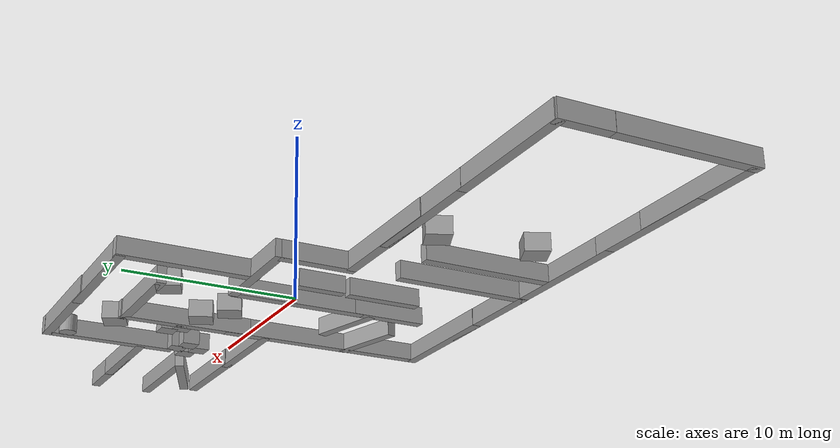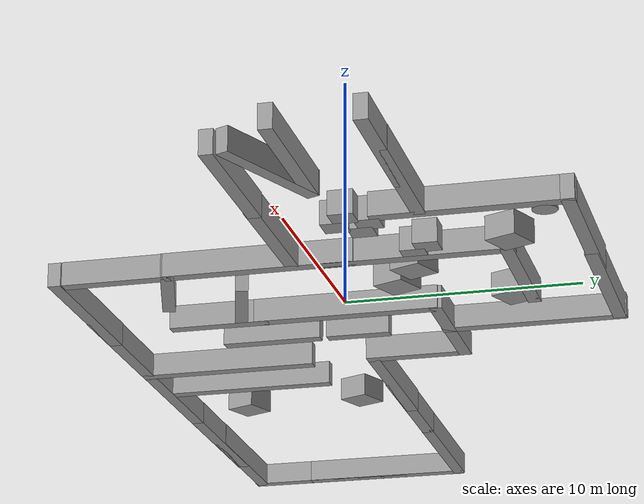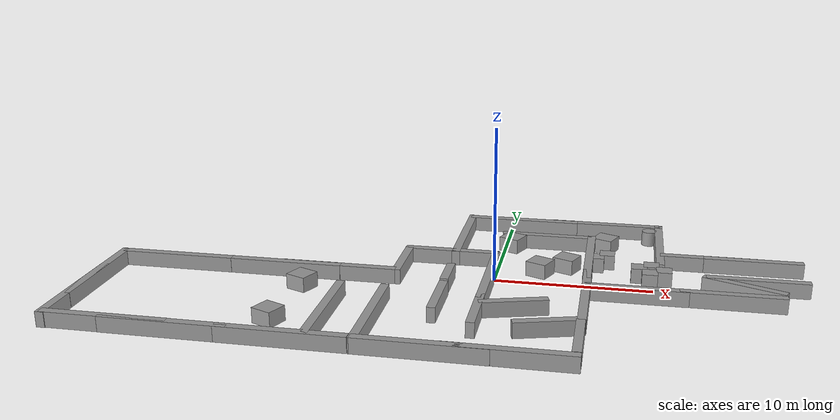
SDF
<?xml version='1.0'?>
<sdf version='1.6'>
  <model name='Maze01'>
    <link name='link_10'>
      <pose frame=''>9.80009 2.02423 9e-06 0 -0 0</pose>
      <inertial>
        <mass>1</mass>
        <inertia>
          <ixx>0.166667</ixx>
          <ixy>0</ixy>
          <ixz>0</ixz>
          <iyy>0.166667</iyy>
          <iyz>0</iyz>
          <izz>0.166667</izz>
        </inertia>
      </inertial>
      <visual name='visual'>
        <pose frame=''>0 0 0 0 -0 0</pose>
        <geometry>
          <box>
            <size>1 1 1</size>
          </box>
        </geometry>
        <material>
          <lighting>1</lighting>
          <script>
            <uri>file://media/materials/scripts/gazebo.material</uri>
            <name>Gazebo/Grey</name>
          </script>
          <ambient>0.3 0.3 0.3 1</ambient>
          <diffuse>0.7 0.7 0.7 1</diffuse>
          <specular>0.01 0.01 0.01 1</specular>
          <emissive>0 0 0 1</emissive>
        </material>
        <transparency>0</transparency>
        <cast_shadows>1</cast_shadows>
      </visual>
      <collision name='collision'>
        <laser_retro>0</laser_retro>
        <max_contacts>10</max_contacts>
        <pose frame=''>0 0 0 0 -0 0</pose>
        <geometry>
          <box>
            <size>1 1 1</size>
          </box>
        </geometry>
        <surface>
          <friction>
            <ode>
              <mu>1</mu>
              <mu2>1</mu2>
              <fdir1>0 0 0</fdir1>
              <slip1>0</slip1>
              <slip2>0</slip2>
            </ode>
            <torsional>
              <coefficient>1</coefficient>
              <patch_radius>0</patch_radius>
              <surface_radius>0</surface_radius>
              <use_patch_radius>1</use_patch_radius>
              <ode>
                <slip>0</slip>
              </ode>
            </torsional>
          </friction>
          <bounce>
            <restitution_coefficient>0</restitution_coefficient>
            <threshold>1e+06</threshold>
          </bounce>
          <contact>
            <collide_without_contact>0</collide_without_contact>
            <collide_without_contact_bitmask>1</collide_without_contact_bitmask>
            <collide_bitmask>1</collide_bitmask>
            <ode>
              <soft_cfm>0</soft_cfm>
              <soft_erp>0.2</soft_erp>
              <kp>1e+13</kp>
              <kd>1</kd>
              <max_vel>0.01</max_vel>
              <min_depth>0</min_depth>
            </ode>
            <bullet>
              <split_impulse>1</split_impulse>
              <split_impulse_penetration_threshold>-0.01</split_impulse_penetration_threshold>
              <soft_cfm>0</soft_cfm>
              <soft_erp>0.2</soft_erp>
              <kp>1e+13</kp>
              <kd>1</kd>
            </bullet>
          </contact>
        </surface>
      </collision>
    </link>
    <link name='link_11'>
      <pose frame=''>6.31823 4.34711 9e-06 0 -0 0</pose>
      <inertial>
        <mass>1</mass>
        <inertia>
          <ixx>0.166667</ixx>
          <ixy>0</ixy>
          <ixz>0</ixz>
          <iyy>0.166667</iyy>
          <iyz>0</iyz>
          <izz>0.166667</izz>
        </inertia>
      </inertial>
      <visual name='visual'>
        <pose frame=''>0 0 0 0 -0 0</pose>
        <geometry>
          <box>
            <size>1 1 1</size>
          </box>
        </geometry>
        <material>
          <lighting>1</lighting>
          <script>
            <uri>file://media/materials/scripts/gazebo.material</uri>
            <name>Gazebo/Grey</name>
          </script>
          <ambient>0.3 0.3 0.3 1</ambient>
          <diffuse>0.7 0.7 0.7 1</diffuse>
          <specular>0.01 0.01 0.01 1</specular>
          <emissive>0 0 0 1</emissive>
        </material>
        <transparency>0</transparency>
        <cast_shadows>1</cast_shadows>
      </visual>
      <collision name='collision'>
        <laser_retro>0</laser_retro>
        <max_contacts>10</max_contacts>
        <pose frame=''>0 0 0 0 -0 0</pose>
        <geometry>
          <box>
            <size>1 1 1</size>
          </box>
        </geometry>
        <surface>
          <friction>
            <ode>
              <mu>1</mu>
              <mu2>1</mu2>
              <fdir1>0 0 0</fdir1>
              <slip1>0</slip1>
              <slip2>0</slip2>
            </ode>
            <torsional>
              <coefficient>1</coefficient>
              <patch_radius>0</patch_radius>
              <surface_radius>0</surface_radius>
              <use_patch_radius>1</use_patch_radius>
              <ode>
                <slip>0</slip>
              </ode>
            </torsional>
          </friction>
          <bounce>
            <restitution_coefficient>0</restitution_coefficient>
            <threshold>1e+06</threshold>
          </bounce>
          <contact>
            <collide_without_contact>0</collide_without_contact>
            <collide_without_contact_bitmask>1</collide_without_contact_bitmask>
            <collide_bitmask>1</collide_bitmask>
            <ode>
              <soft_cfm>0</soft_cfm>
              <soft_erp>0.2</soft_erp>
              <kp>1e+13</kp>
              <kd>1</kd>
              <max_vel>0.01</max_vel>
              <min_depth>0</min_depth>
            </ode>
            <bullet>
              <split_impulse>1</split_impulse>
              <split_impulse_penetration_threshold>-0.01</split_impulse_penetration_threshold>
              <soft_cfm>0</soft_cfm>
              <soft_erp>0.2</soft_erp>
              <kp>1e+13</kp>
              <kd>1</kd>
            </bullet>
          </contact>
        </surface>
      </collision>
    </link>
    <link name='link_12'>
      <pose frame=''>7.00494 5.00129 9e-06 0 -0 0</pose>
      <inertial>
        <mass>1</mass>
        <inertia>
          <ixx>0.166667</ixx>
          <ixy>0</ixy>
          <ixz>0</ixz>
          <iyy>0.166667</iyy>
          <iyz>0</iyz>
          <izz>0.166667</izz>
        </inertia>
      </inertial>
      <visual name='visual'>
        <pose frame=''>0 0 0 0 -0 0</pose>
        <geometry>
          <box>
            <size>1 1 1</size>
          </box>
        </geometry>
        <material>
          <lighting>1</lighting>
          <script>
            <uri>file://media/materials/scripts/gazebo.material</uri>
            <name>Gazebo/Grey</name>
          </script>
          <ambient>0.3 0.3 0.3 1</ambient>
          <diffuse>0.7 0.7 0.7 1</diffuse>
          <specular>0.01 0.01 0.01 1</specular>
          <emissive>0 0 0 1</emissive>
        </material>
        <transparency>0</transparency>
        <cast_shadows>1</cast_shadows>
      </visual>
      <collision name='collision'>
        <laser_retro>0</laser_retro>
        <max_contacts>10</max_contacts>
        <pose frame=''>0 0 0 0 -0 0</pose>
        <geometry>
          <box>
            <size>1 1 1</size>
          </box>
        </geometry>
        <surface>
          <friction>
            <ode>
              <mu>1</mu>
              <mu2>1</mu2>
              <fdir1>0 0 0</fdir1>
              <slip1>0</slip1>
              <slip2>0</slip2>
            </ode>
            <torsional>
              <coefficient>1</coefficient>
              <patch_radius>0</patch_radius>
              <surface_radius>0</surface_radius>
              <use_patch_radius>1</use_patch_radius>
              <ode>
                <slip>0</slip>
              </ode>
            </torsional>
          </friction>
          <bounce>
            <restitution_coefficient>0</restitution_coefficient>
            <threshold>1e+06</threshold>
          </bounce>
          <contact>
            <collide_without_contact>0</collide_without_contact>
            <collide_without_contact_bitmask>1</collide_without_contact_bitmask>
            <collide_bitmask>1</collide_bitmask>
            <ode>
              <soft_cfm>0</soft_cfm>
              <soft_erp>0.2</soft_erp>
              <kp>1e+13</kp>
              <kd>1</kd>
              <max_vel>0.01</max_vel>
              <min_depth>0</min_depth>
            </ode>
            <bullet>
              <split_impulse>1</split_impulse>
              <split_impulse_penetration_threshold>-0.01</split_impulse_penetration_threshold>
              <soft_cfm>0</soft_cfm>
              <soft_erp>0.2</soft_erp>
              <kp>1e+13</kp>
              <kd>1</kd>
            </bullet>
          </contact>
        </surface>
      </collision>
    </link>
    <link name='link_14'>
      <pose frame=''>10.7124 2.54643 9e-06 0 -0 0</pose>
      <inertial>
        <mass>1</mass>
        <inertia>
          <ixx>0.166667</ixx>
          <ixy>0</ixy>
          <ixz>0</ixz>
          <iyy>0.166667</iyy>
          <iyz>0</iyz>
          <izz>0.166667</izz>
        </inertia>
      </inertial>
      <visual name='visual'>
        <pose frame=''>0 0 0 0 -0 0</pose>
        <geometry>
          <box>
            <size>1 1 1</size>
          </box>
        </geometry>
        <material>
          <lighting>1</lighting>
          <script>
            <uri>file://media/materials/scripts/gazebo.material</uri>
            <name>Gazebo/Grey</name>
          </script>
          <ambient>0.3 0.3 0.3 1</ambient>
          <diffuse>0.7 0.7 0.7 1</diffuse>
          <specular>0.01 0.01 0.01 1</specular>
          <emissive>0 0 0 1</emissive>
        </material>
        <transparency>0</transparency>
        <cast_shadows>1</cast_shadows>
      </visual>
      <collision name='collision'>
        <laser_retro>0</laser_retro>
        <max_contacts>10</max_contacts>
        <pose frame=''>0 0 0 0 -0 0</pose>
        <geometry>
          <box>
            <size>1 1 1</size>
          </box>
        </geometry>
        <surface>
          <friction>
            <ode>
              <mu>1</mu>
              <mu2>1</mu2>
              <fdir1>0 0 0</fdir1>
              <slip1>0</slip1>
              <slip2>0</slip2>
            </ode>
            <torsional>
              <coefficient>1</coefficient>
              <patch_radius>0</patch_radius>
              <surface_radius>0</surface_radius>
              <use_patch_radius>1</use_patch_radius>
              <ode>
                <slip>0</slip>
              </ode>
            </torsional>
          </friction>
          <bounce>
            <restitution_coefficient>0</restitution_coefficient>
            <threshold>1e+06</threshold>
          </bounce>
          <contact>
            <collide_without_contact>0</collide_without_contact>
            <collide_without_contact_bitmask>1</collide_without_contact_bitmask>
            <collide_bitmask>1</collide_bitmask>
            <ode>
              <soft_cfm>0</soft_cfm>
              <soft_erp>0.2</soft_erp>
              <kp>1e+13</kp>
              <kd>1</kd>
              <max_vel>0.01</max_vel>
              <min_depth>0</min_depth>
            </ode>
            <bullet>
              <split_impulse>1</split_impulse>
              <split_impulse_penetration_threshold>-0.01</split_impulse_penetration_threshold>
              <soft_cfm>0</soft_cfm>
              <soft_erp>0.2</soft_erp>
              <kp>1e+13</kp>
              <kd>1</kd>
            </bullet>
          </contact>
        </surface>
      </collision>
    </link>
    <link name='link_4_clone_0'>
      <pose frame=''>-21.4897 -10.6297 9e-06 0 -0 0</pose>
      <inertial>
        <mass>4.30693</mass>
        <inertia>
          <ixx>0.46587</ixx>
          <ixy>0</ixy>
          <ixz>0</ixz>
          <iyy>22.6991</iyy>
          <iyz>0</iyz>
          <izz>22.4471</izz>
        </inertia>
        <pose frame=''>0 0 0 0 -0 0</pose>
      </inertial>
      <visual name='visual'>
        <pose frame=''>0 0 0 0 -0 0</pose>
        <geometry>
          <box>
            <size>7.88951 0.545905 1</size>
          </box>
        </geometry>
        <material>
          <lighting>1</lighting>
          <script>
            <uri>file://media/materials/scripts/gazebo.material</uri>
            <name>Gazebo/Grey</name>
          </script>
          <ambient>0.3 0.3 0.3 1</ambient>
          <diffuse>0.7 0.7 0.7 1</diffuse>
          <specular>0.01 0.01 0.01 1</specular>
          <emissive>0 0 0 1</emissive>
          <shader type='pixel'/>
        </material>
        <transparency>0</transparency>
        <cast_shadows>1</cast_shadows>
      </visual>
      <collision name='collision'>
        <laser_retro>0</laser_retro>
        <max_contacts>10</max_contacts>
        <pose frame=''>0 0 0 0 -0 0</pose>
        <geometry>
          <box>
            <size>7.88951 0.545905 1</size>
          </box>
        </geometry>
        <surface>
          <friction>
            <ode>
              <mu>1</mu>
              <mu2>1</mu2>
              <fdir1>0 0 0</fdir1>
              <slip1>0</slip1>
              <slip2>0</slip2>
            </ode>
            <torsional>
              <coefficient>1</coefficient>
              <patch_radius>0</patch_radius>
              <surface_radius>0</surface_radius>
              <use_patch_radius>1</use_patch_radius>
              <ode>
                <slip>0</slip>
              </ode>
            </torsional>
          </friction>
          <bounce>
            <restitution_coefficient>0</restitution_coefficient>
            <threshold>1e+06</threshold>
          </bounce>
          <contact>
            <collide_without_contact>0</collide_without_contact>
            <collide_without_contact_bitmask>1</collide_without_contact_bitmask>
            <collide_bitmask>1</collide_bitmask>
            <ode>
              <soft_cfm>0</soft_cfm>
              <soft_erp>0.2</soft_erp>
              <kp>1e+13</kp>
              <kd>1</kd>
              <max_vel>0.01</max_vel>
              <min_depth>0</min_depth>
            </ode>
            <bullet>
              <split_impulse>1</split_impulse>
              <split_impulse_penetration_threshold>-0.01</split_impulse_penetration_threshold>
              <soft_cfm>0</soft_cfm>
              <soft_erp>0.2</soft_erp>
              <kp>1e+13</kp>
              <kd>1</kd>
            </bullet>
          </contact>
        </surface>
      </collision>
    </link>
    <link name='link_4_clone_0_clone'>
      <pose frame=''>-17.8012 -10.6509 9e-06 0 -0 0</pose>
      <inertial>
        <mass>4.30693</mass>
        <inertia>
          <ixx>0.46587</ixx>
          <ixy>0</ixy>
          <ixz>0</ixz>
          <iyy>22.6991</iyy>
          <iyz>0</iyz>
          <izz>22.4471</izz>
        </inertia>
        <pose frame=''>0 0 0 0 -0 0</pose>
      </inertial>
      <visual name='visual'>
        <pose frame=''>0 0 0 0 -0 0</pose>
        <geometry>
          <box>
            <size>7.88951 0.545905 1</size>
          </box>
        </geometry>
        <material>
          <lighting>1</lighting>
          <script>
            <uri>file://media/materials/scripts/gazebo.material</uri>
            <name>Gazebo/Grey</name>
          </script>
          <ambient>0.3 0.3 0.3 1</ambient>
          <diffuse>0.7 0.7 0.7 1</diffuse>
          <specular>0.01 0.01 0.01 1</specular>
          <emissive>0 0 0 1</emissive>
          <shader type='pixel'/>
        </material>
        <transparency>0</transparency>
        <cast_shadows>1</cast_shadows>
      </visual>
      <collision name='collision'>
        <laser_retro>0</laser_retro>
        <max_contacts>10</max_contacts>
        <pose frame=''>0 0 0 0 -0 0</pose>
        <geometry>
          <box>
            <size>7.88951 0.545905 1</size>
          </box>
        </geometry>
        <surface>
          <friction>
            <ode>
              <mu>1</mu>
              <mu2>1</mu2>
              <fdir1>0 0 0</fdir1>
              <slip1>0</slip1>
              <slip2>0</slip2>
            </ode>
            <torsional>
              <coefficient>1</coefficient>
              <patch_radius>0</patch_radius>
              <surface_radius>0</surface_radius>
              <use_patch_radius>1</use_patch_radius>
              <ode>
                <slip>0</slip>
              </ode>
            </torsional>
          </friction>
          <bounce>
            <restitution_coefficient>0</restitution_coefficient>
            <threshold>1e+06</threshold>
          </bounce>
          <contact>
            <collide_without_contact>0</collide_without_contact>
            <collide_without_contact_bitmask>1</collide_without_contact_bitmask>
            <collide_bitmask>1</collide_bitmask>
            <ode>
              <soft_cfm>0</soft_cfm>
              <soft_erp>0.2</soft_erp>
              <kp>1e+13</kp>
              <kd>1</kd>
              <max_vel>0.01</max_vel>
              <min_depth>0</min_depth>
            </ode>
            <bullet>
              <split_impulse>1</split_impulse>
              <split_impulse_penetration_threshold>-0.01</split_impulse_penetration_threshold>
              <soft_cfm>0</soft_cfm>
              <soft_erp>0.2</soft_erp>
              <kp>1e+13</kp>
              <kd>1</kd>
            </bullet>
          </contact>
        </surface>
      </collision>
    </link>
    <link name='link_4_clone_0_clone_clone'>
      <pose frame=''>-21.5718 -0.350427 9e-06 0 -0 0</pose>
      <inertial>
        <mass>4.30693</mass>
        <inertia>
          <ixx>0.46587</ixx>
          <ixy>0</ixy>
          <ixz>0</ixz>
          <iyy>22.6991</iyy>
          <iyz>0</iyz>
          <izz>22.4471</izz>
        </inertia>
        <pose frame=''>0 0 0 0 -0 0</pose>
      </inertial>
      <visual name='visual'>
        <pose frame=''>0 0 0 0 -0 0</pose>
        <geometry>
          <box>
            <size>7.88951 0.545905 1</size>
          </box>
        </geometry>
        <material>
          <lighting>1</lighting>
          <script>
            <uri>file://media/materials/scripts/gazebo.material</uri>
            <name>Gazebo/Grey</name>
          </script>
          <ambient>0.3 0.3 0.3 1</ambient>
          <diffuse>0.7 0.7 0.7 1</diffuse>
          <specular>0.01 0.01 0.01 1</specular>
          <emissive>0 0 0 1</emissive>
          <shader type='pixel'/>
        </material>
        <transparency>0</transparency>
        <cast_shadows>1</cast_shadows>
      </visual>
      <collision name='collision'>
        <laser_retro>0</laser_retro>
        <max_contacts>10</max_contacts>
        <pose frame=''>0 0 0 0 -0 0</pose>
        <geometry>
          <box>
            <size>7.88951 0.545905 1</size>
          </box>
        </geometry>
        <surface>
          <friction>
            <ode>
              <mu>1</mu>
              <mu2>1</mu2>
              <fdir1>0 0 0</fdir1>
              <slip1>0</slip1>
              <slip2>0</slip2>
            </ode>
            <torsional>
              <coefficient>1</coefficient>
              <patch_radius>0</patch_radius>
              <surface_radius>0</surface_radius>
              <use_patch_radius>1</use_patch_radius>
              <ode>
                <slip>0</slip>
              </ode>
            </torsional>
          </friction>
          <bounce>
            <restitution_coefficient>0</restitution_coefficient>
            <threshold>1e+06</threshold>
          </bounce>
          <contact>
            <collide_without_contact>0</collide_without_contact>
            <collide_without_contact_bitmask>1</collide_without_contact_bitmask>
            <collide_bitmask>1</collide_bitmask>
            <ode>
              <soft_cfm>0</soft_cfm>
              <soft_erp>0.2</soft_erp>
              <kp>1e+13</kp>
              <kd>1</kd>
              <max_vel>0.01</max_vel>
              <min_depth>0</min_depth>
            </ode>
            <bullet>
              <split_impulse>1</split_impulse>
              <split_impulse_penetration_threshold>-0.01</split_impulse_penetration_threshold>
              <soft_cfm>0</soft_cfm>
              <soft_erp>0.2</soft_erp>
              <kp>1e+13</kp>
              <kd>1</kd>
            </bullet>
          </contact>
        </surface>
      </collision>
    </link>
    <link name='link_4_clone_0_clone_clone_0'>
      <pose frame=''>-14.0594 -0.346312 9e-06 0 -0 0</pose>
      <inertial>
        <mass>4.30693</mass>
        <inertia>
          <ixx>0.46587</ixx>
          <ixy>0</ixy>
          <ixz>0</ixz>
          <iyy>22.6991</iyy>
          <iyz>0</iyz>
          <izz>22.4471</izz>
        </inertia>
        <pose frame=''>0 0 0 0 0 0</pose>
      </inertial>
      <visual name='visual'>
        <pose frame=''>0 0 0 0 -0 0</pose>
        <geometry>
          <box>
            <size>7.88951 0.545905 1</size>
          </box>
        </geometry>
        <material>
          <lighting>1</lighting>
          <script>
            <uri>file://media/materials/scripts/gazebo.material</uri>
            <name>Gazebo/Grey</name>
          </script>
          <ambient>0.3 0.3 0.3 1</ambient>
          <diffuse>0.7 0.7 0.7 1</diffuse>
          <specular>0.01 0.01 0.01 1</specular>
          <emissive>0 0 0 1</emissive>
          <shader type='pixel'/>
        </material>
        <transparency>0</transparency>
        <cast_shadows>1</cast_shadows>
      </visual>
      <collision name='collision'>
        <laser_retro>0</laser_retro>
        <max_contacts>10</max_contacts>
        <pose frame=''>0 0 0 0 -0 0</pose>
        <geometry>
          <box>
            <size>7.88951 0.545905 1</size>
          </box>
        </geometry>
        <surface>
          <friction>
            <ode>
              <mu>1</mu>
              <mu2>1</mu2>
              <fdir1>0 0 0</fdir1>
              <slip1>0</slip1>
              <slip2>0</slip2>
            </ode>
            <torsional>
              <coefficient>1</coefficient>
              <patch_radius>0</patch_radius>
              <surface_radius>0</surface_radius>
              <use_patch_radius>1</use_patch_radius>
              <ode>
                <slip>0</slip>
              </ode>
            </torsional>
          </friction>
          <bounce>
            <restitution_coefficient>0</restitution_coefficient>
            <threshold>1e+06</threshold>
          </bounce>
          <contact>
            <collide_without_contact>0</collide_without_contact>
            <collide_without_contact_bitmask>1</collide_without_contact_bitmask>
            <collide_bitmask>1</collide_bitmask>
            <ode>
              <soft_cfm>0</soft_cfm>
              <soft_erp>0.2</soft_erp>
              <kp>1e+13</kp>
              <kd>1</kd>
              <max_vel>0.01</max_vel>
              <min_depth>0</min_depth>
            </ode>
            <bullet>
              <split_impulse>1</split_impulse>
              <split_impulse_penetration_threshold>-0.01</split_impulse_penetration_threshold>
              <soft_cfm>0</soft_cfm>
              <soft_erp>0.2</soft_erp>
              <kp>1e+13</kp>
              <kd>1</kd>
            </bullet>
          </contact>
        </surface>
      </collision>
    </link>
    <link name='link_4_clone_0_clone_clone_1'>
      <pose frame=''>-10.6658 -10.6545 9e-06 0 -0 0</pose>
      <inertial>
        <mass>4.30693</mass>
        <inertia>
          <ixx>0.46587</ixx>
          <ixy>0</ixy>
          <ixz>0</ixz>
          <iyy>22.6991</iyy>
          <iyz>0</iyz>
          <izz>22.4471</izz>
        </inertia>
        <pose frame=''>0 0 0 0 -0 0</pose>
      </inertial>
      <visual name='visual'>
        <pose frame=''>0 0 0 0 -0 0</pose>
        <geometry>
          <box>
            <size>7.88951 0.545905 1</size>
          </box>
        </geometry>
        <material>
          <lighting>1</lighting>
          <script>
            <uri>file://media/materials/scripts/gazebo.material</uri>
            <name>Gazebo/Grey</name>
          </script>
          <ambient>0.3 0.3 0.3 1</ambient>
          <diffuse>0.7 0.7 0.7 1</diffuse>
          <specular>0.01 0.01 0.01 1</specular>
          <emissive>0 0 0 1</emissive>
          <shader type='pixel'/>
        </material>
        <transparency>0</transparency>
        <cast_shadows>1</cast_shadows>
      </visual>
      <collision name='collision'>
        <laser_retro>0</laser_retro>
        <max_contacts>10</max_contacts>
        <pose frame=''>0 0 0 0 -0 0</pose>
        <geometry>
          <box>
            <size>7.88951 0.545905 1</size>
          </box>
        </geometry>
        <surface>
          <friction>
            <ode>
              <mu>1</mu>
              <mu2>1</mu2>
              <fdir1>0 0 0</fdir1>
              <slip1>0</slip1>
              <slip2>0</slip2>
            </ode>
            <torsional>
              <coefficient>1</coefficient>
              <patch_radius>0</patch_radius>
              <surface_radius>0</surface_radius>
              <use_patch_radius>1</use_patch_radius>
              <ode>
                <slip>0</slip>
              </ode>
            </torsional>
          </friction>
          <bounce>
            <restitution_coefficient>0</restitution_coefficient>
            <threshold>1e+06</threshold>
          </bounce>
          <contact>
            <collide_without_contact>0</collide_without_contact>
            <collide_without_contact_bitmask>1</collide_without_contact_bitmask>
            <collide_bitmask>1</collide_bitmask>
            <ode>
              <soft_cfm>0</soft_cfm>
              <soft_erp>0.2</soft_erp>
              <kp>1e+13</kp>
              <kd>1</kd>
              <max_vel>0.01</max_vel>
              <min_depth>0</min_depth>
            </ode>
            <bullet>
              <split_impulse>1</split_impulse>
              <split_impulse_penetration_threshold>-0.01</split_impulse_penetration_threshold>
              <soft_cfm>0</soft_cfm>
              <soft_erp>0.2</soft_erp>
              <kp>1e+13</kp>
              <kd>1</kd>
            </bullet>
          </contact>
        </surface>
      </collision>
    </link>
    <link name='link_4_clone_0_clone_clone_1_clone'>
      <pose frame=''>-3.41756 3.78222 9e-06 0 -0 0</pose>
      <inertial>
        <mass>3.50538</mass>
        <inertia>
          <ixx>0.379168</ixx>
          <ixy>0</ixy>
          <ixz>0</ixz>
          <iyy>12.3366</iyy>
          <iyz>0</iyz>
          <izz>12.1315</izz>
        </inertia>
        <pose frame=''>0 0 0 0 -0 0</pose>
      </inertial>
      <visual name='visual'>
        <pose frame=''>0 0 0 0 -0 0</pose>
        <geometry>
          <box>
            <size>6.42122 0.545905 1</size>
          </box>
        </geometry>
        <material>
          <lighting>1</lighting>
          <script>
            <uri>file://media/materials/scripts/gazebo.material</uri>
            <name>Gazebo/Grey</name>
          </script>
          <ambient>0.3 0.3 0.3 1</ambient>
          <diffuse>0.7 0.7 0.7 1</diffuse>
          <specular>0.01 0.01 0.01 1</specular>
          <emissive>0 0 0 1</emissive>
          <shader type='pixel'/>
        </material>
        <transparency>0</transparency>
        <cast_shadows>1</cast_shadows>
      </visual>
      <collision name='collision'>
        <laser_retro>0</laser_retro>
        <max_contacts>10</max_contacts>
        <pose frame=''>0 0 0 0 -0 0</pose>
        <geometry>
          <box>
            <size>6.42122 0.545905 1</size>
          </box>
        </geometry>
        <surface>
          <friction>
            <ode>
              <mu>1</mu>
              <mu2>1</mu2>
              <fdir1>0 0 0</fdir1>
              <slip1>0</slip1>
              <slip2>0</slip2>
            </ode>
            <torsional>
              <coefficient>1</coefficient>
              <patch_radius>0</patch_radius>
              <surface_radius>0</surface_radius>
              <use_patch_radius>1</use_patch_radius>
              <ode>
                <slip>0</slip>
              </ode>
            </torsional>
          </friction>
          <bounce>
            <restitution_coefficient>0</restitution_coefficient>
            <threshold>1e+06</threshold>
          </bounce>
          <contact>
            <collide_without_contact>0</collide_without_contact>
            <collide_without_contact_bitmask>1</collide_without_contact_bitmask>
            <collide_bitmask>1</collide_bitmask>
            <ode>
              <soft_cfm>0</soft_cfm>
              <soft_erp>0.2</soft_erp>
              <kp>1e+13</kp>
              <kd>1</kd>
              <max_vel>0.01</max_vel>
              <min_depth>0</min_depth>
            </ode>
            <bullet>
              <split_impulse>1</split_impulse>
              <split_impulse_penetration_threshold>-0.01</split_impulse_penetration_threshold>
              <soft_cfm>0</soft_cfm>
              <soft_erp>0.2</soft_erp>
              <kp>1e+13</kp>
              <kd>1</kd>
            </bullet>
          </contact>
        </surface>
      </collision>
    </link>
    <link name='link_4_clone_0_clone_clone_1_clone_0'>
      <pose frame=''>-2.67814 -10.6624 9e-06 0 -0 0</pose>
      <inertial>
        <mass>4.30693</mass>
        <inertia>
          <ixx>0.46587</ixx>
          <ixy>0</ixy>
          <ixz>0</ixz>
          <iyy>22.6991</iyy>
          <iyz>0</iyz>
          <izz>22.4471</izz>
        </inertia>
        <pose frame=''>0 0 0 0 -0 0</pose>
      </inertial>
      <visual name='visual'>
        <pose frame=''>0 0 0 0 -0 0</pose>
        <geometry>
          <box>
            <size>7.88951 0.545905 1</size>
          </box>
        </geometry>
        <material>
          <lighting>1</lighting>
          <script>
            <uri>file://media/materials/scripts/gazebo.material</uri>
            <name>Gazebo/Grey</name>
          </script>
          <ambient>0.3 0.3 0.3 1</ambient>
          <diffuse>0.7 0.7 0.7 1</diffuse>
          <specular>0.01 0.01 0.01 1</specular>
          <emissive>0 0 0 1</emissive>
          <shader type='pixel'/>
        </material>
        <transparency>0</transparency>
        <cast_shadows>1</cast_shadows>
      </visual>
      <collision name='collision'>
        <laser_retro>0</laser_retro>
        <max_contacts>10</max_contacts>
        <pose frame=''>0 0 0 0 -0 0</pose>
        <geometry>
          <box>
            <size>7.88951 0.545905 1</size>
          </box>
        </geometry>
        <surface>
          <friction>
            <ode>
              <mu>1</mu>
              <mu2>1</mu2>
              <fdir1>0 0 0</fdir1>
              <slip1>0</slip1>
              <slip2>0</slip2>
            </ode>
            <torsional>
              <coefficient>1</coefficient>
              <patch_radius>0</patch_radius>
              <surface_radius>0</surface_radius>
              <use_patch_radius>1</use_patch_radius>
              <ode>
                <slip>0</slip>
              </ode>
            </torsional>
          </friction>
          <bounce>
            <restitution_coefficient>0</restitution_coefficient>
            <threshold>1e+06</threshold>
          </bounce>
          <contact>
            <collide_without_contact>0</collide_without_contact>
            <collide_without_contact_bitmask>1</collide_without_contact_bitmask>
            <collide_bitmask>1</collide_bitmask>
            <ode>
              <soft_cfm>0</soft_cfm>
              <soft_erp>0.2</soft_erp>
              <kp>1e+13</kp>
              <kd>1</kd>
              <max_vel>0.01</max_vel>
              <min_depth>0</min_depth>
            </ode>
            <bullet>
              <split_impulse>1</split_impulse>
              <split_impulse_penetration_threshold>-0.01</split_impulse_penetration_threshold>
              <soft_cfm>0</soft_cfm>
              <soft_erp>0.2</soft_erp>
              <kp>1e+13</kp>
              <kd>1</kd>
            </bullet>
          </contact>
        </surface>
      </collision>
    </link>
    <link name='link_4_clone_0_clone_clone_1_clone_0_clone'>
      <pose frame=''>2.19804 -10.643 9e-06 0 -0 0</pose>
      <inertial>
        <mass>4.30693</mass>
        <inertia>
          <ixx>0.46587</ixx>
          <ixy>0</ixy>
          <ixz>0</ixz>
          <iyy>22.6991</iyy>
          <iyz>0</iyz>
          <izz>22.4471</izz>
        </inertia>
        <pose frame=''>0 0 0 0 -0 0</pose>
      </inertial>
      <visual name='visual'>
        <pose frame=''>0 0 0 0 -0 0</pose>
        <geometry>
          <box>
            <size>7.88951 0.545905 1</size>
          </box>
        </geometry>
        <material>
          <lighting>1</lighting>
          <script>
            <uri>file://media/materials/scripts/gazebo.material</uri>
            <name>Gazebo/Grey</name>
          </script>
          <ambient>0.3 0.3 0.3 1</ambient>
          <diffuse>0.7 0.7 0.7 1</diffuse>
          <specular>0.01 0.01 0.01 1</specular>
          <emissive>0 0 0 1</emissive>
          <shader type='pixel'/>
        </material>
        <transparency>0</transparency>
        <cast_shadows>1</cast_shadows>
      </visual>
      <collision name='collision'>
        <laser_retro>0</laser_retro>
        <max_contacts>10</max_contacts>
        <pose frame=''>0 0 0 0 -0 0</pose>
        <geometry>
          <box>
            <size>7.88951 0.545905 1</size>
          </box>
        </geometry>
        <surface>
          <friction>
            <ode>
              <mu>1</mu>
              <mu2>1</mu2>
              <fdir1>0 0 0</fdir1>
              <slip1>0</slip1>
              <slip2>0</slip2>
            </ode>
            <torsional>
              <coefficient>1</coefficient>
              <patch_radius>0</patch_radius>
              <surface_radius>0</surface_radius>
              <use_patch_radius>1</use_patch_radius>
              <ode>
                <slip>0</slip>
              </ode>
            </torsional>
          </friction>
          <bounce>
            <restitution_coefficient>0</restitution_coefficient>
            <threshold>1e+06</threshold>
          </bounce>
          <contact>
            <collide_without_contact>0</collide_without_contact>
            <collide_without_contact_bitmask>1</collide_without_contact_bitmask>
            <collide_bitmask>1</collide_bitmask>
            <ode>
              <soft_cfm>0</soft_cfm>
              <soft_erp>0.2</soft_erp>
              <kp>1e+13</kp>
              <kd>1</kd>
              <max_vel>0.01</max_vel>
              <min_depth>0</min_depth>
            </ode>
            <bullet>
              <split_impulse>1</split_impulse>
              <split_impulse_penetration_threshold>-0.01</split_impulse_penetration_threshold>
              <soft_cfm>0</soft_cfm>
              <soft_erp>0.2</soft_erp>
              <kp>1e+13</kp>
              <kd>1</kd>
            </bullet>
          </contact>
        </surface>
      </collision>
    </link>
    <link name='link_4_clone_0_clone_clone_1_clone_0_clone_0'>
      <pose frame=''>0.695253 11.0512 9e-06 0 -0 0</pose>
      <inertial>
        <mass>4.30693</mass>
        <inertia>
          <ixx>0.46587</ixx>
          <ixy>0</ixy>
          <ixz>0</ixz>
          <iyy>22.6991</iyy>
          <iyz>0</iyz>
          <izz>22.4471</izz>
        </inertia>
        <pose frame=''>0 0 0 0 -0 0</pose>
      </inertial>
      <visual name='visual'>
        <pose frame=''>0 0 0 0 -0 0</pose>
        <geometry>
          <box>
            <size>7.88951 0.545905 1</size>
          </box>
        </geometry>
        <material>
          <lighting>1</lighting>
          <script>
            <uri>file://media/materials/scripts/gazebo.material</uri>
            <name>Gazebo/Grey</name>
          </script>
          <ambient>0.3 0.3 0.3 1</ambient>
          <diffuse>0.7 0.7 0.7 1</diffuse>
          <specular>0.01 0.01 0.01 1</specular>
          <emissive>0 0 0 1</emissive>
          <shader type='pixel'/>
        </material>
        <transparency>0</transparency>
        <cast_shadows>1</cast_shadows>
      </visual>
      <collision name='collision'>
        <laser_retro>0</laser_retro>
        <max_contacts>10</max_contacts>
        <pose frame=''>0 0 0 0 -0 0</pose>
        <geometry>
          <box>
            <size>7.88951 0.545905 1</size>
          </box>
        </geometry>
        <surface>
          <friction>
            <ode>
              <mu>1</mu>
              <mu2>1</mu2>
              <fdir1>0 0 0</fdir1>
              <slip1>0</slip1>
              <slip2>0</slip2>
            </ode>
            <torsional>
              <coefficient>1</coefficient>
              <patch_radius>0</patch_radius>
              <surface_radius>0</surface_radius>
              <use_patch_radius>1</use_patch_radius>
              <ode>
                <slip>0</slip>
              </ode>
            </torsional>
          </friction>
          <bounce>
            <restitution_coefficient>0</restitution_coefficient>
            <threshold>1e+06</threshold>
          </bounce>
          <contact>
            <collide_without_contact>0</collide_without_contact>
            <collide_without_contact_bitmask>1</collide_without_contact_bitmask>
            <collide_bitmask>1</collide_bitmask>
            <ode>
              <soft_cfm>0</soft_cfm>
              <soft_erp>0.2</soft_erp>
              <kp>1e+13</kp>
              <kd>1</kd>
              <max_vel>0.01</max_vel>
              <min_depth>0</min_depth>
            </ode>
            <bullet>
              <split_impulse>1</split_impulse>
              <split_impulse_penetration_threshold>-0.01</split_impulse_penetration_threshold>
              <soft_cfm>0</soft_cfm>
              <soft_erp>0.2</soft_erp>
              <kp>1e+13</kp>
              <kd>1</kd>
            </bullet>
          </contact>
        </surface>
      </collision>
    </link>
    <link name='link_4_clone_0_clone_clone_1_clone_0_clone_0_clone'>
      <pose frame=''>6.79233 11.1081 9e-06 0 -0 0</pose>
      <inertial>
        <mass>4.30693</mass>
        <inertia>
          <ixx>0.46587</ixx>
          <ixy>0</ixy>
          <ixz>0</ixz>
          <iyy>22.6991</iyy>
          <iyz>0</iyz>
          <izz>22.4471</izz>
        </inertia>
        <pose frame=''>0 0 0 0 -0 0</pose>
      </inertial>
      <visual name='visual'>
        <pose frame=''>0 0 0 0 -0 0</pose>
        <geometry>
          <box>
            <size>7.88951 0.545905 1</size>
          </box>
        </geometry>
        <material>
          <lighting>1</lighting>
          <script>
            <uri>file://media/materials/scripts/gazebo.material</uri>
            <name>Gazebo/Grey</name>
          </script>
          <ambient>0.3 0.3 0.3 1</ambient>
          <diffuse>0.7 0.7 0.7 1</diffuse>
          <specular>0.01 0.01 0.01 1</specular>
          <emissive>0 0 0 1</emissive>
          <shader type='pixel'/>
        </material>
        <transparency>0</transparency>
        <cast_shadows>1</cast_shadows>
      </visual>
      <collision name='collision'>
        <laser_retro>0</laser_retro>
        <max_contacts>10</max_contacts>
        <pose frame=''>0 0 0 0 -0 0</pose>
        <geometry>
          <box>
            <size>7.88951 0.545905 1</size>
          </box>
        </geometry>
        <surface>
          <friction>
            <ode>
              <mu>1</mu>
              <mu2>1</mu2>
              <fdir1>0 0 0</fdir1>
              <slip1>0</slip1>
              <slip2>0</slip2>
            </ode>
            <torsional>
              <coefficient>1</coefficient>
              <patch_radius>0</patch_radius>
              <surface_radius>0</surface_radius>
              <use_patch_radius>1</use_patch_radius>
              <ode>
                <slip>0</slip>
              </ode>
            </torsional>
          </friction>
          <bounce>
            <restitution_coefficient>0</restitution_coefficient>
            <threshold>1e+06</threshold>
          </bounce>
          <contact>
            <collide_without_contact>0</collide_without_contact>
            <collide_without_contact_bitmask>1</collide_without_contact_bitmask>
            <collide_bitmask>1</collide_bitmask>
            <ode>
              <soft_cfm>0</soft_cfm>
              <soft_erp>0.2</soft_erp>
              <kp>1e+13</kp>
              <kd>1</kd>
              <max_vel>0.01</max_vel>
              <min_depth>0</min_depth>
            </ode>
            <bullet>
              <split_impulse>1</split_impulse>
              <split_impulse_penetration_threshold>-0.01</split_impulse_penetration_threshold>
              <soft_cfm>0</soft_cfm>
              <soft_erp>0.2</soft_erp>
              <kp>1e+13</kp>
              <kd>1</kd>
            </bullet>
          </contact>
        </surface>
      </collision>
    </link>
    <link name='link_4_clone_0_clone_clone_1_clone_clone'>
      <pose frame=''>2.76705 7.92871 9e-06 0 -0 0</pose>
      <inertial>
        <mass>3.50538</mass>
        <inertia>
          <ixx>0.379168</ixx>
          <ixy>0</ixy>
          <ixz>0</ixz>
          <iyy>12.3366</iyy>
          <iyz>0</iyz>
          <izz>12.1315</izz>
        </inertia>
        <pose frame=''>0 0 0 0 -0 0</pose>
      </inertial>
      <visual name='visual'>
        <pose frame=''>0 0 0 0 -0 0</pose>
        <geometry>
          <box>
            <size>6.42122 0.545905 1</size>
          </box>
        </geometry>
        <material>
          <lighting>1</lighting>
          <script>
            <uri>file://media/materials/scripts/gazebo.material</uri>
            <name>Gazebo/Grey</name>
          </script>
          <ambient>0.3 0.3 0.3 1</ambient>
          <diffuse>0.7 0.7 0.7 1</diffuse>
          <specular>0.01 0.01 0.01 1</specular>
          <emissive>0 0 0 1</emissive>
          <shader type='pixel'/>
        </material>
        <transparency>0</transparency>
        <cast_shadows>1</cast_shadows>
      </visual>
      <collision name='collision'>
        <laser_retro>0</laser_retro>
        <max_contacts>10</max_contacts>
        <pose frame=''>0 0 0 0 -0 0</pose>
        <geometry>
          <box>
            <size>6.42122 0.545905 1</size>
          </box>
        </geometry>
        <surface>
          <friction>
            <ode>
              <mu>1</mu>
              <mu2>1</mu2>
              <fdir1>0 0 0</fdir1>
              <slip1>0</slip1>
              <slip2>0</slip2>
            </ode>
            <torsional>
              <coefficient>1</coefficient>
              <patch_radius>0</patch_radius>
              <surface_radius>0</surface_radius>
              <use_patch_radius>1</use_patch_radius>
              <ode>
                <slip>0</slip>
              </ode>
            </torsional>
          </friction>
          <bounce>
            <restitution_coefficient>0</restitution_coefficient>
            <threshold>1e+06</threshold>
          </bounce>
          <contact>
            <collide_without_contact>0</collide_without_contact>
            <collide_without_contact_bitmask>1</collide_without_contact_bitmask>
            <collide_bitmask>1</collide_bitmask>
            <ode>
              <soft_cfm>0</soft_cfm>
              <soft_erp>0.2</soft_erp>
              <kp>1e+13</kp>
              <kd>1</kd>
              <max_vel>0.01</max_vel>
              <min_depth>0</min_depth>
            </ode>
            <bullet>
              <split_impulse>1</split_impulse>
              <split_impulse_penetration_threshold>-0.01</split_impulse_penetration_threshold>
              <soft_cfm>0</soft_cfm>
              <soft_erp>0.2</soft_erp>
              <kp>1e+13</kp>
              <kd>1</kd>
            </bullet>
          </contact>
        </surface>
      </collision>
    </link>
    <link name='link_4_clone_0_clone_clone_1_clone_clone_0'>
      <pose frame=''>8.96944 -0.687018 9e-06 0 -0 0</pose>
      <inertial>
        <mass>3.50538</mass>
        <inertia>
          <ixx>0.379168</ixx>
          <ixy>0</ixy>
          <ixz>0</ixz>
          <iyy>12.3366</iyy>
          <iyz>0</iyz>
          <izz>12.1315</izz>
        </inertia>
        <pose frame=''>0 0 0 0 -0 0</pose>
      </inertial>
      <visual name='visual'>
        <pose frame=''>0 0 0 0 -0 0</pose>
        <geometry>
          <box>
            <size>6.42122 0.545905 1</size>
          </box>
        </geometry>
        <material>
          <lighting>1</lighting>
          <script>
            <uri>file://media/materials/scripts/gazebo.material</uri>
            <name>Gazebo/Grey</name>
          </script>
          <ambient>0.3 0.3 0.3 1</ambient>
          <diffuse>0.7 0.7 0.7 1</diffuse>
          <specular>0.01 0.01 0.01 1</specular>
          <emissive>0 0 0 1</emissive>
          <shader type='pixel'/>
        </material>
        <transparency>0</transparency>
        <cast_shadows>1</cast_shadows>
      </visual>
      <collision name='collision'>
        <laser_retro>0</laser_retro>
        <max_contacts>10</max_contacts>
        <pose frame=''>0 0 0 0 -0 0</pose>
        <geometry>
          <box>
            <size>6.42122 0.545905 1</size>
          </box>
        </geometry>
        <surface>
          <friction>
            <ode>
              <mu>1</mu>
              <mu2>1</mu2>
              <fdir1>0 0 0</fdir1>
              <slip1>0</slip1>
              <slip2>0</slip2>
            </ode>
            <torsional>
              <coefficient>1</coefficient>
              <patch_radius>0</patch_radius>
              <surface_radius>0</surface_radius>
              <use_patch_radius>1</use_patch_radius>
              <ode>
                <slip>0</slip>
              </ode>
            </torsional>
          </friction>
          <bounce>
            <restitution_coefficient>0</restitution_coefficient>
            <threshold>1e+06</threshold>
          </bounce>
          <contact>
            <collide_without_contact>0</collide_without_contact>
            <collide_without_contact_bitmask>1</collide_without_contact_bitmask>
            <collide_bitmask>1</collide_bitmask>
            <ode>
              <soft_cfm>0</soft_cfm>
              <soft_erp>0.2</soft_erp>
              <kp>1e+13</kp>
              <kd>1</kd>
              <max_vel>0.01</max_vel>
              <min_depth>0</min_depth>
            </ode>
            <bullet>
              <split_impulse>1</split_impulse>
              <split_impulse_penetration_threshold>-0.01</split_impulse_penetration_threshold>
              <soft_cfm>0</soft_cfm>
              <soft_erp>0.2</soft_erp>
              <kp>1e+13</kp>
              <kd>1</kd>
            </bullet>
          </contact>
        </surface>
      </collision>
    </link>
    <link name='link_4_clone_0_clone_clone_1_clone_clone_0_clone'>
      <pose frame=''>13.7042 5.43273 9e-06 0 -0 0</pose>
      <inertial>
        <mass>3.50538</mass>
        <inertia>
          <ixx>0.379168</ixx>
          <ixy>0</ixy>
          <ixz>0</ixz>
          <iyy>12.3366</iyy>
          <iyz>0</iyz>
          <izz>12.1315</izz>
        </inertia>
        <pose frame=''>0 0 0 0 -0 0</pose>
      </inertial>
      <visual name='visual'>
        <pose frame=''>0 0 0 0 -0 0</pose>
        <geometry>
          <box>
            <size>6.42122 0.545905 1</size>
          </box>
        </geometry>
        <material>
          <lighting>1</lighting>
          <script>
            <uri>file://media/materials/scripts/gazebo.material</uri>
            <name>Gazebo/Grey</name>
          </script>
          <ambient>0.3 0.3 0.3 1</ambient>
          <diffuse>0.7 0.7 0.7 1</diffuse>
          <specular>0.01 0.01 0.01 1</specular>
          <emissive>0 0 0 1</emissive>
          <shader type='pixel'/>
        </material>
        <transparency>0</transparency>
        <cast_shadows>1</cast_shadows>
      </visual>
      <collision name='collision'>
        <laser_retro>0</laser_retro>
        <max_contacts>10</max_contacts>
        <pose frame=''>0 0 0 0 -0 0</pose>
        <geometry>
          <box>
            <size>6.42122 0.545905 1</size>
          </box>
        </geometry>
        <surface>
          <friction>
            <ode>
              <mu>1</mu>
              <mu2>1</mu2>
              <fdir1>0 0 0</fdir1>
              <slip1>0</slip1>
              <slip2>0</slip2>
            </ode>
            <torsional>
              <coefficient>1</coefficient>
              <patch_radius>0</patch_radius>
              <surface_radius>0</surface_radius>
              <use_patch_radius>1</use_patch_radius>
              <ode>
                <slip>0</slip>
              </ode>
            </torsional>
          </friction>
          <bounce>
            <restitution_coefficient>0</restitution_coefficient>
            <threshold>1e+06</threshold>
          </bounce>
          <contact>
            <collide_without_contact>0</collide_without_contact>
            <collide_without_contact_bitmask>1</collide_without_contact_bitmask>
            <collide_bitmask>1</collide_bitmask>
            <ode>
              <soft_cfm>0</soft_cfm>
              <soft_erp>0.2</soft_erp>
              <kp>1e+13</kp>
              <kd>1</kd>
              <max_vel>0.01</max_vel>
              <min_depth>0</min_depth>
            </ode>
            <bullet>
              <split_impulse>1</split_impulse>
              <split_impulse_penetration_threshold>-0.01</split_impulse_penetration_threshold>
              <soft_cfm>0</soft_cfm>
              <soft_erp>0.2</soft_erp>
              <kp>1e+13</kp>
              <kd>1</kd>
            </bullet>
          </contact>
        </surface>
      </collision>
    </link>
    <link name='link_4_clone_0_clone_clone_1_clone_clone_0_clone_0'>
      <pose frame=''>16.5218 2.00661 9e-06 0 -0 0</pose>
      <inertial>
        <mass>3.50538</mass>
        <inertia>
          <ixx>0.379168</ixx>
          <ixy>0</ixy>
          <ixz>0</ixz>
          <iyy>12.3366</iyy>
          <iyz>0</iyz>
          <izz>12.1315</izz>
        </inertia>
        <pose frame=''>0 0 0 0 -0 0</pose>
      </inertial>
      <visual name='visual'>
        <pose frame=''>0 0 0 0 -0 0</pose>
        <geometry>
          <box>
            <size>6.42122 0.545905 1</size>
          </box>
        </geometry>
        <material>
          <lighting>1</lighting>
          <script>
            <uri>file://media/materials/scripts/gazebo.material</uri>
            <name>Gazebo/Grey</name>
          </script>
          <ambient>0.3 0.3 0.3 1</ambient>
          <diffuse>0.7 0.7 0.7 1</diffuse>
          <specular>0.01 0.01 0.01 1</specular>
          <emissive>0 0 0 1</emissive>
          <shader type='pixel'/>
        </material>
        <transparency>0</transparency>
        <cast_shadows>1</cast_shadows>
      </visual>
      <collision name='collision'>
        <laser_retro>0</laser_retro>
        <max_contacts>10</max_contacts>
        <pose frame=''>0 0 0 0 -0 0</pose>
        <geometry>
          <box>
            <size>6.42122 0.545905 1</size>
          </box>
        </geometry>
        <surface>
          <friction>
            <ode>
              <mu>1</mu>
              <mu2>1</mu2>
              <fdir1>0 0 0</fdir1>
              <slip1>0</slip1>
              <slip2>0</slip2>
            </ode>
            <torsional>
              <coefficient>1</coefficient>
              <patch_radius>0</patch_radius>
              <surface_radius>0</surface_radius>
              <use_patch_radius>1</use_patch_radius>
              <ode>
                <slip>0</slip>
              </ode>
            </torsional>
          </friction>
          <bounce>
            <restitution_coefficient>0</restitution_coefficient>
            <threshold>1e+06</threshold>
          </bounce>
          <contact>
            <collide_without_contact>0</collide_without_contact>
            <collide_without_contact_bitmask>1</collide_without_contact_bitmask>
            <collide_bitmask>1</collide_bitmask>
            <ode>
              <soft_cfm>0</soft_cfm>
              <soft_erp>0.2</soft_erp>
              <kp>1e+13</kp>
              <kd>1</kd>
              <max_vel>0.01</max_vel>
              <min_depth>0</min_depth>
            </ode>
            <bullet>
              <split_impulse>1</split_impulse>
              <split_impulse_penetration_threshold>-0.01</split_impulse_penetration_threshold>
              <soft_cfm>0</soft_cfm>
              <soft_erp>0.2</soft_erp>
              <kp>1e+13</kp>
              <kd>1</kd>
            </bullet>
          </contact>
        </surface>
      </collision>
    </link>
    <link name='link_4_clone_0_clone_clone_1_clone_clone_0_clone_1'>
      <pose frame=''>16.5551 5.42013 9e-06 0 -0 0</pose>
      <inertial>
        <mass>3.50538</mass>
        <inertia>
          <ixx>0.379168</ixx>
          <ixy>0</ixy>
          <ixz>0</ixz>
          <iyy>12.3366</iyy>
          <iyz>0</iyz>
          <izz>12.1315</izz>
        </inertia>
        <pose frame=''>0 0 0 0 -0 0</pose>
      </inertial>
      <visual name='visual'>
        <pose frame=''>0 0 0 0 -0 0</pose>
        <geometry>
          <box>
            <size>6.42122 0.545905 1</size>
          </box>
        </geometry>
        <material>
          <lighting>1</lighting>
          <script>
            <uri>file://media/materials/scripts/gazebo.material</uri>
            <name>Gazebo/Grey</name>
          </script>
          <ambient>0.3 0.3 0.3 1</ambient>
          <diffuse>0.7 0.7 0.7 1</diffuse>
          <specular>0.01 0.01 0.01 1</specular>
          <emissive>0 0 0 1</emissive>
          <shader type='pixel'/>
        </material>
        <transparency>0</transparency>
        <cast_shadows>1</cast_shadows>
      </visual>
      <collision name='collision'>
        <laser_retro>0</laser_retro>
        <max_contacts>10</max_contacts>
        <pose frame=''>0 0 0 0 -0 0</pose>
        <geometry>
          <box>
            <size>6.42122 0.545905 1</size>
          </box>
        </geometry>
        <surface>
          <friction>
            <ode>
              <mu>1</mu>
              <mu2>1</mu2>
              <fdir1>0 0 0</fdir1>
              <slip1>0</slip1>
              <slip2>0</slip2>
            </ode>
            <torsional>
              <coefficient>1</coefficient>
              <patch_radius>0</patch_radius>
              <surface_radius>0</surface_radius>
              <use_patch_radius>1</use_patch_radius>
              <ode>
                <slip>0</slip>
              </ode>
            </torsional>
          </friction>
          <bounce>
            <restitution_coefficient>0</restitution_coefficient>
            <threshold>1e+06</threshold>
          </bounce>
          <contact>
            <collide_without_contact>0</collide_without_contact>
            <collide_without_contact_bitmask>1</collide_without_contact_bitmask>
            <collide_bitmask>1</collide_bitmask>
            <ode>
              <soft_cfm>0</soft_cfm>
              <soft_erp>0.2</soft_erp>
              <kp>1e+13</kp>
              <kd>1</kd>
              <max_vel>0.01</max_vel>
              <min_depth>0</min_depth>
            </ode>
            <bullet>
              <split_impulse>1</split_impulse>
              <split_impulse_penetration_threshold>-0.01</split_impulse_penetration_threshold>
              <soft_cfm>0</soft_cfm>
              <soft_erp>0.2</soft_erp>
              <kp>1e+13</kp>
              <kd>1</kd>
            </bullet>
          </contact>
        </surface>
      </collision>
    </link>
    <link name='link_4_clone_0_clone_clone_1_clone_clone_1'>
      <pose frame=''>14.7931 -0.66198 9e-06 0 -0 0</pose>
      <inertial>
        <mass>3.50538</mass>
        <inertia>
          <ixx>0.379168</ixx>
          <ixy>0</ixy>
          <ixz>0</ixz>
          <iyy>12.3366</iyy>
          <iyz>0</iyz>
          <izz>12.1315</izz>
        </inertia>
        <pose frame=''>0 0 0 0 -0 0</pose>
      </inertial>
      <visual name='visual'>
        <pose frame=''>0 0 0 0 -0 0</pose>
        <geometry>
          <box>
            <size>6.42122 0.545905 1</size>
          </box>
        </geometry>
        <material>
          <lighting>1</lighting>
          <script>
            <uri>file://media/materials/scripts/gazebo.material</uri>
            <name>Gazebo/Grey</name>
          </script>
          <ambient>0.3 0.3 0.3 1</ambient>
          <diffuse>0.7 0.7 0.7 1</diffuse>
          <specular>0.01 0.01 0.01 1</specular>
          <emissive>0 0 0 1</emissive>
          <shader type='pixel'/>
        </material>
        <transparency>0</transparency>
        <cast_shadows>1</cast_shadows>
      </visual>
      <collision name='collision'>
        <laser_retro>0</laser_retro>
        <max_contacts>10</max_contacts>
        <pose frame=''>0 0 0 0 -0 0</pose>
        <geometry>
          <box>
            <size>6.42122 0.545905 1</size>
          </box>
        </geometry>
        <surface>
          <friction>
            <ode>
              <mu>1</mu>
              <mu2>1</mu2>
              <fdir1>0 0 0</fdir1>
              <slip1>0</slip1>
              <slip2>0</slip2>
            </ode>
            <torsional>
              <coefficient>1</coefficient>
              <patch_radius>0</patch_radius>
              <surface_radius>0</surface_radius>
              <use_patch_radius>1</use_patch_radius>
              <ode>
                <slip>0</slip>
              </ode>
            </torsional>
          </friction>
          <bounce>
            <restitution_coefficient>0</restitution_coefficient>
            <threshold>1e+06</threshold>
          </bounce>
          <contact>
            <collide_without_contact>0</collide_without_contact>
            <collide_without_contact_bitmask>1</collide_without_contact_bitmask>
            <collide_bitmask>1</collide_bitmask>
            <ode>
              <soft_cfm>0</soft_cfm>
              <soft_erp>0.2</soft_erp>
              <kp>1e+13</kp>
              <kd>1</kd>
              <max_vel>0.01</max_vel>
              <min_depth>0</min_depth>
            </ode>
            <bullet>
              <split_impulse>1</split_impulse>
              <split_impulse_penetration_threshold>-0.01</split_impulse_penetration_threshold>
              <soft_cfm>0</soft_cfm>
              <soft_erp>0.2</soft_erp>
              <kp>1e+13</kp>
              <kd>1</kd>
            </bullet>
          </contact>
        </surface>
      </collision>
    </link>
    <link name='link_4_clone_0_clone_clone_2'>
      <pose frame=''>-10.3733 -0.31076 9e-06 0 -0 0</pose>
      <inertial>
        <mass>4.30693</mass>
        <inertia>
          <ixx>0.46587</ixx>
          <ixy>0</ixy>
          <ixz>0</ixz>
          <iyy>22.6991</iyy>
          <iyz>0</iyz>
          <izz>22.4471</izz>
        </inertia>
        <pose frame=''>0 0 0 0 -0 0</pose>
      </inertial>
      <visual name='visual'>
        <pose frame=''>0 0 0 0 -0 0</pose>
        <geometry>
          <box>
            <size>7.88951 0.545905 1</size>
          </box>
        </geometry>
        <material>
          <lighting>1</lighting>
          <script>
            <uri>file://media/materials/scripts/gazebo.material</uri>
            <name>Gazebo/Grey</name>
          </script>
          <ambient>0.3 0.3 0.3 1</ambient>
          <diffuse>0.7 0.7 0.7 1</diffuse>
          <specular>0.01 0.01 0.01 1</specular>
          <emissive>0 0 0 1</emissive>
          <shader type='pixel'/>
        </material>
        <transparency>0</transparency>
        <cast_shadows>1</cast_shadows>
      </visual>
      <collision name='collision'>
        <laser_retro>0</laser_retro>
        <max_contacts>10</max_contacts>
        <pose frame=''>0 0 0 0 -0 0</pose>
        <geometry>
          <box>
            <size>7.88951 0.545905 1</size>
          </box>
        </geometry>
        <surface>
          <friction>
            <ode>
              <mu>1</mu>
              <mu2>1</mu2>
              <fdir1>0 0 0</fdir1>
              <slip1>0</slip1>
              <slip2>0</slip2>
            </ode>
            <torsional>
              <coefficient>1</coefficient>
              <patch_radius>0</patch_radius>
              <surface_radius>0</surface_radius>
              <use_patch_radius>1</use_patch_radius>
              <ode>
                <slip>0</slip>
              </ode>
            </torsional>
          </friction>
          <bounce>
            <restitution_coefficient>0</restitution_coefficient>
            <threshold>1e+06</threshold>
          </bounce>
          <contact>
            <collide_without_contact>0</collide_without_contact>
            <collide_without_contact_bitmask>1</collide_without_contact_bitmask>
            <collide_bitmask>1</collide_bitmask>
            <ode>
              <soft_cfm>0</soft_cfm>
              <soft_erp>0.2</soft_erp>
              <kp>1e+13</kp>
              <kd>1</kd>
              <max_vel>0.01</max_vel>
              <min_depth>0</min_depth>
            </ode>
            <bullet>
              <split_impulse>1</split_impulse>
              <split_impulse_penetration_threshold>-0.01</split_impulse_penetration_threshold>
              <soft_cfm>0</soft_cfm>
              <soft_erp>0.2</soft_erp>
              <kp>1e+13</kp>
              <kd>1</kd>
            </bullet>
          </contact>
        </surface>
      </collision>
    </link>
    <link name='link_4_clone_1'>
      <pose frame=''>-25.335 -7.00928 9e-06 0 0 -1.56693</pose>
      <inertial>
        <mass>4.30693</mass>
        <inertia>
          <ixx>0.46587</ixx>
          <ixy>0</ixy>
          <ixz>0</ixz>
          <iyy>22.6991</iyy>
          <iyz>0</iyz>
          <izz>22.4471</izz>
        </inertia>
        <pose frame=''>0 0 0 0 -0 0</pose>
      </inertial>
      <visual name='visual'>
        <pose frame=''>0 0 0 0 -0 0</pose>
        <geometry>
          <box>
            <size>7.88951 0.545905 1</size>
          </box>
        </geometry>
        <material>
          <lighting>1</lighting>
          <script>
            <uri>file://media/materials/scripts/gazebo.material</uri>
            <name>Gazebo/Grey</name>
          </script>
          <ambient>0.3 0.3 0.3 1</ambient>
          <diffuse>0.7 0.7 0.7 1</diffuse>
          <specular>0.01 0.01 0.01 1</specular>
          <emissive>0 0 0 1</emissive>
          <shader type='pixel'/>
        </material>
        <transparency>0</transparency>
        <cast_shadows>1</cast_shadows>
      </visual>
      <collision name='collision'>
        <laser_retro>0</laser_retro>
        <max_contacts>10</max_contacts>
        <pose frame=''>0 0 0 0 -0 0</pose>
        <geometry>
          <box>
            <size>7.88951 0.545905 1</size>
          </box>
        </geometry>
        <surface>
          <friction>
            <ode>
              <mu>1</mu>
              <mu2>1</mu2>
              <fdir1>0 0 0</fdir1>
              <slip1>0</slip1>
              <slip2>0</slip2>
            </ode>
            <torsional>
              <coefficient>1</coefficient>
              <patch_radius>0</patch_radius>
              <surface_radius>0</surface_radius>
              <use_patch_radius>1</use_patch_radius>
              <ode>
                <slip>0</slip>
              </ode>
            </torsional>
          </friction>
          <bounce>
            <restitution_coefficient>0</restitution_coefficient>
            <threshold>1e+06</threshold>
          </bounce>
          <contact>
            <collide_without_contact>0</collide_without_contact>
            <collide_without_contact_bitmask>1</collide_without_contact_bitmask>
            <collide_bitmask>1</collide_bitmask>
            <ode>
              <soft_cfm>0</soft_cfm>
              <soft_erp>0.2</soft_erp>
              <kp>1e+13</kp>
              <kd>1</kd>
              <max_vel>0.01</max_vel>
              <min_depth>0</min_depth>
            </ode>
            <bullet>
              <split_impulse>1</split_impulse>
              <split_impulse_penetration_threshold>-0.01</split_impulse_penetration_threshold>
              <soft_cfm>0</soft_cfm>
              <soft_erp>0.2</soft_erp>
              <kp>1e+13</kp>
              <kd>1</kd>
            </bullet>
          </contact>
        </surface>
      </collision>
    </link>
    <link name='link_4_clone_1_clone'>
      <pose frame=''>-25.3389 -4.07653 9e-06 0 0 -1.56693</pose>
      <inertial>
        <mass>4.30693</mass>
        <inertia>
          <ixx>0.46587</ixx>
          <ixy>0</ixy>
          <ixz>0</ixz>
          <iyy>22.6991</iyy>
          <iyz>0</iyz>
          <izz>22.4471</izz>
        </inertia>
        <pose frame=''>0 0 0 0 -0 0</pose>
      </inertial>
      <visual name='visual'>
        <pose frame=''>0 0 0 0 -0 0</pose>
        <geometry>
          <box>
            <size>7.88951 0.545905 1</size>
          </box>
        </geometry>
        <material>
          <lighting>1</lighting>
          <script>
            <uri>file://media/materials/scripts/gazebo.material</uri>
            <name>Gazebo/Grey</name>
          </script>
          <ambient>0.3 0.3 0.3 1</ambient>
          <diffuse>0.7 0.7 0.7 1</diffuse>
          <specular>0.01 0.01 0.01 1</specular>
          <emissive>0 0 0 1</emissive>
          <shader type='pixel'/>
        </material>
        <transparency>0</transparency>
        <cast_shadows>1</cast_shadows>
      </visual>
      <collision name='collision'>
        <laser_retro>0</laser_retro>
        <max_contacts>10</max_contacts>
        <pose frame=''>0 0 0 0 -0 0</pose>
        <geometry>
          <box>
            <size>7.88951 0.545905 1</size>
          </box>
        </geometry>
        <surface>
          <friction>
            <ode>
              <mu>1</mu>
              <mu2>1</mu2>
              <fdir1>0 0 0</fdir1>
              <slip1>0</slip1>
              <slip2>0</slip2>
            </ode>
            <torsional>
              <coefficient>1</coefficient>
              <patch_radius>0</patch_radius>
              <surface_radius>0</surface_radius>
              <use_patch_radius>1</use_patch_radius>
              <ode>
                <slip>0</slip>
              </ode>
            </torsional>
          </friction>
          <bounce>
            <restitution_coefficient>0</restitution_coefficient>
            <threshold>1e+06</threshold>
          </bounce>
          <contact>
            <collide_without_contact>0</collide_without_contact>
            <collide_without_contact_bitmask>1</collide_without_contact_bitmask>
            <collide_bitmask>1</collide_bitmask>
            <ode>
              <soft_cfm>0</soft_cfm>
              <soft_erp>0.2</soft_erp>
              <kp>1e+13</kp>
              <kd>1</kd>
              <max_vel>0.01</max_vel>
              <min_depth>0</min_depth>
            </ode>
            <bullet>
              <split_impulse>1</split_impulse>
              <split_impulse_penetration_threshold>-0.01</split_impulse_penetration_threshold>
              <soft_cfm>0</soft_cfm>
              <soft_erp>0.2</soft_erp>
              <kp>1e+13</kp>
              <kd>1</kd>
            </bullet>
          </contact>
        </surface>
      </collision>
    </link>
    <link name='link_4_clone_1_clone_0'>
      <pose frame=''>-9.31294 -6.93569 9e-06 0 0 -1.56693</pose>
      <inertial>
        <mass>4.30693</mass>
        <inertia>
          <ixx>0.46587</ixx>
          <ixy>0</ixy>
          <ixz>0</ixz>
          <iyy>22.6991</iyy>
          <iyz>0</iyz>
          <izz>22.4471</izz>
        </inertia>
        <pose frame=''>0 0 0 0 -0 0</pose>
      </inertial>
      <visual name='visual'>
        <pose frame=''>0 0 0 0 -0 0</pose>
        <geometry>
          <box>
            <size>7.88951 0.545905 1</size>
          </box>
        </geometry>
        <material>
          <lighting>1</lighting>
          <script>
            <uri>file://media/materials/scripts/gazebo.material</uri>
            <name>Gazebo/Grey</name>
          </script>
          <ambient>0.3 0.3 0.3 1</ambient>
          <diffuse>0.7 0.7 0.7 1</diffuse>
          <specular>0.01 0.01 0.01 1</specular>
          <emissive>0 0 0 1</emissive>
          <shader type='pixel'/>
        </material>
        <transparency>0</transparency>
        <cast_shadows>1</cast_shadows>
      </visual>
      <collision name='collision'>
        <laser_retro>0</laser_retro>
        <max_contacts>10</max_contacts>
        <pose frame=''>0 0 0 0 -0 0</pose>
        <geometry>
          <box>
            <size>7.88951 0.545905 1</size>
          </box>
        </geometry>
        <surface>
          <friction>
            <ode>
              <mu>1</mu>
              <mu2>1</mu2>
              <fdir1>0 0 0</fdir1>
              <slip1>0</slip1>
              <slip2>0</slip2>
            </ode>
            <torsional>
              <coefficient>1</coefficient>
              <patch_radius>0</patch_radius>
              <surface_radius>0</surface_radius>
              <use_patch_radius>1</use_patch_radius>
              <ode>
                <slip>0</slip>
              </ode>
            </torsional>
          </friction>
          <bounce>
            <restitution_coefficient>0</restitution_coefficient>
            <threshold>1e+06</threshold>
          </bounce>
          <contact>
            <collide_without_contact>0</collide_without_contact>
            <collide_without_contact_bitmask>1</collide_without_contact_bitmask>
            <collide_bitmask>1</collide_bitmask>
            <ode>
              <soft_cfm>0</soft_cfm>
              <soft_erp>0.2</soft_erp>
              <kp>1e+13</kp>
              <kd>1</kd>
              <max_vel>0.01</max_vel>
              <min_depth>0</min_depth>
            </ode>
            <bullet>
              <split_impulse>1</split_impulse>
              <split_impulse_penetration_threshold>-0.01</split_impulse_penetration_threshold>
              <soft_cfm>0</soft_cfm>
              <soft_erp>0.2</soft_erp>
              <kp>1e+13</kp>
              <kd>1</kd>
            </bullet>
          </contact>
        </surface>
      </collision>
    </link>
    <link name='link_4_clone_1_clone_1'>
      <pose frame=''>-6.43669 -6.98415 9e-06 0 0 -1.56693</pose>
      <inertial>
        <mass>4.30693</mass>
        <inertia>
          <ixx>0.46587</ixx>
          <ixy>0</ixy>
          <ixz>0</ixz>
          <iyy>22.6991</iyy>
          <iyz>0</iyz>
          <izz>22.4471</izz>
        </inertia>
        <pose frame=''>0 0 0 0 -0 0</pose>
      </inertial>
      <visual name='visual'>
        <pose frame=''>0 0 0 0 -0 0</pose>
        <geometry>
          <box>
            <size>7.88951 0.545905 1</size>
          </box>
        </geometry>
        <material>
          <lighting>1</lighting>
          <script>
            <uri>file://media/materials/scripts/gazebo.material</uri>
            <name>Gazebo/Grey</name>
          </script>
          <ambient>0.3 0.3 0.3 1</ambient>
          <diffuse>0.7 0.7 0.7 1</diffuse>
          <specular>0.01 0.01 0.01 1</specular>
          <emissive>0 0 0 1</emissive>
          <shader type='pixel'/>
        </material>
        <transparency>0</transparency>
        <cast_shadows>1</cast_shadows>
      </visual>
      <collision name='collision'>
        <laser_retro>0</laser_retro>
        <max_contacts>10</max_contacts>
        <pose frame=''>0 0 0 0 -0 0</pose>
        <geometry>
          <box>
            <size>7.88951 0.545905 1</size>
          </box>
        </geometry>
        <surface>
          <friction>
            <ode>
              <mu>1</mu>
              <mu2>1</mu2>
              <fdir1>0 0 0</fdir1>
              <slip1>0</slip1>
              <slip2>0</slip2>
            </ode>
            <torsional>
              <coefficient>1</coefficient>
              <patch_radius>0</patch_radius>
              <surface_radius>0</surface_radius>
              <use_patch_radius>1</use_patch_radius>
              <ode>
                <slip>0</slip>
              </ode>
            </torsional>
          </friction>
          <bounce>
            <restitution_coefficient>0</restitution_coefficient>
            <threshold>1e+06</threshold>
          </bounce>
          <contact>
            <collide_without_contact>0</collide_without_contact>
            <collide_without_contact_bitmask>1</collide_without_contact_bitmask>
            <collide_bitmask>1</collide_bitmask>
            <ode>
              <soft_cfm>0</soft_cfm>
              <soft_erp>0.2</soft_erp>
              <kp>1e+13</kp>
              <kd>1</kd>
              <max_vel>0.01</max_vel>
              <min_depth>0</min_depth>
            </ode>
            <bullet>
              <split_impulse>1</split_impulse>
              <split_impulse_penetration_threshold>-0.01</split_impulse_penetration_threshold>
              <soft_cfm>0</soft_cfm>
              <soft_erp>0.2</soft_erp>
              <kp>1e+13</kp>
              <kd>1</kd>
            </bullet>
          </contact>
        </surface>
      </collision>
    </link>
    <link name='link_4_clone_1_clone_1_clone'>
      <pose frame=''>-6.35585 1.56416 9e-06 0 0 -1.56693</pose>
      <inertial>
        <mass>2.3361</mass>
        <inertia>
          <ixx>0.25269</ixx>
          <ixy>0</ixy>
          <ixz>0</ixz>
          <iyy>3.75965</iyy>
          <iyz>0</iyz>
          <izz>3.62299</izz>
        </inertia>
        <pose frame=''>0 0 0 0 -0 0</pose>
      </inertial>
      <visual name='visual'>
        <pose frame=''>0 0 0 0 -0 0</pose>
        <geometry>
          <box>
            <size>4.27931 0.545905 1</size>
          </box>
        </geometry>
        <material>
          <lighting>1</lighting>
          <script>
            <uri>file://media/materials/scripts/gazebo.material</uri>
            <name>Gazebo/Grey</name>
          </script>
          <ambient>0.3 0.3 0.3 1</ambient>
          <diffuse>0.7 0.7 0.7 1</diffuse>
          <specular>0.01 0.01 0.01 1</specular>
          <emissive>0 0 0 1</emissive>
          <shader type='pixel'/>
        </material>
        <transparency>0</transparency>
        <cast_shadows>1</cast_shadows>
      </visual>
      <collision name='collision'>
        <laser_retro>0</laser_retro>
        <max_contacts>10</max_contacts>
        <pose frame=''>0 0 0 0 -0 0</pose>
        <geometry>
          <box>
            <size>4.27931 0.545905 1</size>
          </box>
        </geometry>
        <surface>
          <friction>
            <ode>
              <mu>1</mu>
              <mu2>1</mu2>
              <fdir1>0 0 0</fdir1>
              <slip1>0</slip1>
              <slip2>0</slip2>
            </ode>
            <torsional>
              <coefficient>1</coefficient>
              <patch_radius>0</patch_radius>
              <surface_radius>0</surface_radius>
              <use_patch_radius>1</use_patch_radius>
              <ode>
                <slip>0</slip>
              </ode>
            </torsional>
          </friction>
          <bounce>
            <restitution_coefficient>0</restitution_coefficient>
            <threshold>1e+06</threshold>
          </bounce>
          <contact>
            <collide_without_contact>0</collide_without_contact>
            <collide_without_contact_bitmask>1</collide_without_contact_bitmask>
            <collide_bitmask>1</collide_bitmask>
            <ode>
              <soft_cfm>0</soft_cfm>
              <soft_erp>0.2</soft_erp>
              <kp>1e+13</kp>
              <kd>1</kd>
              <max_vel>0.01</max_vel>
              <min_depth>0</min_depth>
            </ode>
            <bullet>
              <split_impulse>1</split_impulse>
              <split_impulse_penetration_threshold>-0.01</split_impulse_penetration_threshold>
              <soft_cfm>0</soft_cfm>
              <soft_erp>0.2</soft_erp>
              <kp>1e+13</kp>
              <kd>1</kd>
            </bullet>
          </contact>
        </surface>
      </collision>
    </link>
    <link name='link_4_clone_1_clone_1_clone_0'>
      <pose frame=''>-0.36051 -0.054697 9e-06 0 0 -1.56693</pose>
      <inertial>
        <mass>4.30693</mass>
        <inertia>
          <ixx>0.46587</ixx>
          <ixy>0</ixy>
          <ixz>0</ixz>
          <iyy>22.6991</iyy>
          <iyz>0</iyz>
          <izz>22.4471</izz>
        </inertia>
        <pose frame=''>0 0 0 0 -0 0</pose>
      </inertial>
      <visual name='visual'>
        <pose frame=''>0 0 0 0 -0 0</pose>
        <geometry>
          <box>
            <size>7.88951 0.545905 1</size>
          </box>
        </geometry>
        <material>
          <lighting>1</lighting>
          <script>
            <uri>file://media/materials/scripts/gazebo.material</uri>
            <name>Gazebo/Grey</name>
          </script>
          <ambient>0.3 0.3 0.3 1</ambient>
          <diffuse>0.7 0.7 0.7 1</diffuse>
          <specular>0.01 0.01 0.01 1</specular>
          <emissive>0 0 0 1</emissive>
          <shader type='pixel'/>
        </material>
        <transparency>0</transparency>
        <cast_shadows>1</cast_shadows>
      </visual>
      <collision name='collision'>
        <laser_retro>0</laser_retro>
        <max_contacts>10</max_contacts>
        <pose frame=''>0 0 0 0 -0 0</pose>
        <geometry>
          <box>
            <size>7.88951 0.545905 1</size>
          </box>
        </geometry>
        <surface>
          <friction>
            <ode>
              <mu>1</mu>
              <mu2>1</mu2>
              <fdir1>0 0 0</fdir1>
              <slip1>0</slip1>
              <slip2>0</slip2>
            </ode>
            <torsional>
              <coefficient>1</coefficient>
              <patch_radius>0</patch_radius>
              <surface_radius>0</surface_radius>
              <use_patch_radius>1</use_patch_radius>
              <ode>
                <slip>0</slip>
              </ode>
            </torsional>
          </friction>
          <bounce>
            <restitution_coefficient>0</restitution_coefficient>
            <threshold>1e+06</threshold>
          </bounce>
          <contact>
            <collide_without_contact>0</collide_without_contact>
            <collide_without_contact_bitmask>1</collide_without_contact_bitmask>
            <collide_bitmask>1</collide_bitmask>
            <ode>
              <soft_cfm>0</soft_cfm>
              <soft_erp>0.2</soft_erp>
              <kp>1e+13</kp>
              <kd>1</kd>
              <max_vel>0.01</max_vel>
              <min_depth>0</min_depth>
            </ode>
            <bullet>
              <split_impulse>1</split_impulse>
              <split_impulse_penetration_threshold>-0.01</split_impulse_penetration_threshold>
              <soft_cfm>0</soft_cfm>
              <soft_erp>0.2</soft_erp>
              <kp>1e+13</kp>
              <kd>1</kd>
            </bullet>
          </contact>
        </surface>
      </collision>
    </link>
    <link name='link_4_clone_1_clone_1_clone_0_clone'>
      <pose frame=''>5.88859 -2.1218 9e-06 0 0 -1.56693</pose>
      <inertial>
        <mass>4.30693</mass>
        <inertia>
          <ixx>0.46587</ixx>
          <ixy>0</ixy>
          <ixz>0</ixz>
          <iyy>22.6991</iyy>
          <iyz>0</iyz>
          <izz>22.4471</izz>
        </inertia>
        <pose frame=''>0 0 0 0 -0 0</pose>
      </inertial>
      <visual name='visual'>
        <pose frame=''>0 0 0 0 -0 0</pose>
        <geometry>
          <box>
            <size>7.88951 0.545905 1</size>
          </box>
        </geometry>
        <material>
          <lighting>1</lighting>
          <script>
            <uri>file://media/materials/scripts/gazebo.material</uri>
            <name>Gazebo/Grey</name>
          </script>
          <ambient>0.3 0.3 0.3 1</ambient>
          <diffuse>0.7 0.7 0.7 1</diffuse>
          <specular>0.01 0.01 0.01 1</specular>
          <emissive>0 0 0 1</emissive>
          <shader type='pixel'/>
        </material>
        <transparency>0</transparency>
        <cast_shadows>1</cast_shadows>
      </visual>
      <collision name='collision'>
        <laser_retro>0</laser_retro>
        <max_contacts>10</max_contacts>
        <pose frame=''>0 0 0 0 -0 0</pose>
        <geometry>
          <box>
            <size>7.88951 0.545905 1</size>
          </box>
        </geometry>
        <surface>
          <friction>
            <ode>
              <mu>1</mu>
              <mu2>1</mu2>
              <fdir1>0 0 0</fdir1>
              <slip1>0</slip1>
              <slip2>0</slip2>
            </ode>
            <torsional>
              <coefficient>1</coefficient>
              <patch_radius>0</patch_radius>
              <surface_radius>0</surface_radius>
              <use_patch_radius>1</use_patch_radius>
              <ode>
                <slip>0</slip>
              </ode>
            </torsional>
          </friction>
          <bounce>
            <restitution_coefficient>0</restitution_coefficient>
            <threshold>1e+06</threshold>
          </bounce>
          <contact>
            <collide_without_contact>0</collide_without_contact>
            <collide_without_contact_bitmask>1</collide_without_contact_bitmask>
            <collide_bitmask>1</collide_bitmask>
            <ode>
              <soft_cfm>0</soft_cfm>
              <soft_erp>0.2</soft_erp>
              <kp>1e+13</kp>
              <kd>1</kd>
              <max_vel>0.01</max_vel>
              <min_depth>0</min_depth>
            </ode>
            <bullet>
              <split_impulse>1</split_impulse>
              <split_impulse_penetration_threshold>-0.01</split_impulse_penetration_threshold>
              <soft_cfm>0</soft_cfm>
              <soft_erp>0.2</soft_erp>
              <kp>1e+13</kp>
              <kd>1</kd>
            </bullet>
          </contact>
        </surface>
      </collision>
    </link>
    <link name='link_4_clone_1_clone_1_clone_0_clone_clone'>
      <pose frame=''>10.4715 7.44804 9e-06 0 0 -1.56693</pose>
      <inertial>
        <mass>4.30693</mass>
        <inertia>
          <ixx>0.46587</ixx>
          <ixy>0</ixy>
          <ixz>0</ixz>
          <iyy>22.6991</iyy>
          <iyz>0</iyz>
          <izz>22.4471</izz>
        </inertia>
        <pose frame=''>0 0 0 0 -0 0</pose>
      </inertial>
      <visual name='visual'>
        <pose frame=''>0 0 0 0 -0 0</pose>
        <geometry>
          <box>
            <size>7.88951 0.545905 1</size>
          </box>
        </geometry>
        <material>
          <lighting>1</lighting>
          <script>
            <uri>file://media/materials/scripts/gazebo.material</uri>
            <name>Gazebo/Grey</name>
          </script>
          <ambient>0.3 0.3 0.3 1</ambient>
          <diffuse>0.7 0.7 0.7 1</diffuse>
          <specular>0.01 0.01 0.01 1</specular>
          <emissive>0 0 0 1</emissive>
          <shader type='pixel'/>
        </material>
        <transparency>0</transparency>
        <cast_shadows>1</cast_shadows>
      </visual>
      <collision name='collision'>
        <laser_retro>0</laser_retro>
        <max_contacts>10</max_contacts>
        <pose frame=''>0 0 0 0 -0 0</pose>
        <geometry>
          <box>
            <size>7.88951 0.545905 1</size>
          </box>
        </geometry>
        <surface>
          <friction>
            <ode>
              <mu>1</mu>
              <mu2>1</mu2>
              <fdir1>0 0 0</fdir1>
              <slip1>0</slip1>
              <slip2>0</slip2>
            </ode>
            <torsional>
              <coefficient>1</coefficient>
              <patch_radius>0</patch_radius>
              <surface_radius>0</surface_radius>
              <use_patch_radius>1</use_patch_radius>
              <ode>
                <slip>0</slip>
              </ode>
            </torsional>
          </friction>
          <bounce>
            <restitution_coefficient>0</restitution_coefficient>
            <threshold>1e+06</threshold>
          </bounce>
          <contact>
            <collide_without_contact>0</collide_without_contact>
            <collide_without_contact_bitmask>1</collide_without_contact_bitmask>
            <collide_bitmask>1</collide_bitmask>
            <ode>
              <soft_cfm>0</soft_cfm>
              <soft_erp>0.2</soft_erp>
              <kp>1e+13</kp>
              <kd>1</kd>
              <max_vel>0.01</max_vel>
              <min_depth>0</min_depth>
            </ode>
            <bullet>
              <split_impulse>1</split_impulse>
              <split_impulse_penetration_threshold>-0.01</split_impulse_penetration_threshold>
              <soft_cfm>0</soft_cfm>
              <soft_erp>0.2</soft_erp>
              <kp>1e+13</kp>
              <kd>1</kd>
            </bullet>
          </contact>
        </surface>
      </collision>
    </link>
    <link name='link_4_clone_1_clone_1_clone_1'>
      <pose frame=''>5.82858 4.32024 9e-06 0 0 -1.56693</pose>
      <inertial>
        <mass>4.30693</mass>
        <inertia>
          <ixx>0.46587</ixx>
          <ixy>0</ixy>
          <ixz>0</ixz>
          <iyy>22.6991</iyy>
          <iyz>0</iyz>
          <izz>22.4471</izz>
        </inertia>
        <pose frame=''>0 0 0 0 -0 0</pose>
      </inertial>
      <visual name='visual'>
        <pose frame=''>0 0 0 0 -0 0</pose>
        <geometry>
          <box>
            <size>7.88951 0.545905 1</size>
          </box>
        </geometry>
        <material>
          <lighting>1</lighting>
          <script>
            <uri>file://media/materials/scripts/gazebo.material</uri>
            <name>Gazebo/Grey</name>
          </script>
          <ambient>0.3 0.3 0.3 1</ambient>
          <diffuse>0.7 0.7 0.7 1</diffuse>
          <specular>0.01 0.01 0.01 1</specular>
          <emissive>0 0 0 1</emissive>
          <shader type='pixel'/>
        </material>
        <transparency>0</transparency>
        <cast_shadows>1</cast_shadows>
      </visual>
      <collision name='collision'>
        <laser_retro>0</laser_retro>
        <max_contacts>10</max_contacts>
        <pose frame=''>0 0 0 0 -0 0</pose>
        <geometry>
          <box>
            <size>7.88951 0.545905 1</size>
          </box>
        </geometry>
        <surface>
          <friction>
            <ode>
              <mu>1</mu>
              <mu2>1</mu2>
              <fdir1>0 0 0</fdir1>
              <slip1>0</slip1>
              <slip2>0</slip2>
            </ode>
            <torsional>
              <coefficient>1</coefficient>
              <patch_radius>0</patch_radius>
              <surface_radius>0</surface_radius>
              <use_patch_radius>1</use_patch_radius>
              <ode>
                <slip>0</slip>
              </ode>
            </torsional>
          </friction>
          <bounce>
            <restitution_coefficient>0</restitution_coefficient>
            <threshold>1e+06</threshold>
          </bounce>
          <contact>
            <collide_without_contact>0</collide_without_contact>
            <collide_without_contact_bitmask>1</collide_without_contact_bitmask>
            <collide_bitmask>1</collide_bitmask>
            <ode>
              <soft_cfm>0</soft_cfm>
              <soft_erp>0.2</soft_erp>
              <kp>1e+13</kp>
              <kd>1</kd>
              <max_vel>0.01</max_vel>
              <min_depth>0</min_depth>
            </ode>
            <bullet>
              <split_impulse>1</split_impulse>
              <split_impulse_penetration_threshold>-0.01</split_impulse_penetration_threshold>
              <soft_cfm>0</soft_cfm>
              <soft_erp>0.2</soft_erp>
              <kp>1e+13</kp>
              <kd>1</kd>
            </bullet>
          </contact>
        </surface>
      </collision>
    </link>
    <link name='link_4_clone_1_clone_1_clone_2'>
      <pose frame=''>-3.1358 7.42604 9e-06 0 0 -1.56693</pose>
      <inertial>
        <mass>4.30693</mass>
        <inertia>
          <ixx>0.46587</ixx>
          <ixy>0</ixy>
          <ixz>0</ixz>
          <iyy>22.6991</iyy>
          <iyz>0</iyz>
          <izz>22.4471</izz>
        </inertia>
        <pose frame=''>0 0 0 0 -0 0</pose>
      </inertial>
      <visual name='visual'>
        <pose frame=''>0 0 0 0 -0 0</pose>
        <geometry>
          <box>
            <size>7.88951 0.545905 1</size>
          </box>
        </geometry>
        <material>
          <lighting>1</lighting>
          <script>
            <uri>file://media/materials/scripts/gazebo.material</uri>
            <name>Gazebo/Grey</name>
          </script>
          <ambient>0.3 0.3 0.3 1</ambient>
          <diffuse>0.7 0.7 0.7 1</diffuse>
          <specular>0.01 0.01 0.01 1</specular>
          <emissive>0 0 0 1</emissive>
          <shader type='pixel'/>
        </material>
        <transparency>0</transparency>
        <cast_shadows>1</cast_shadows>
      </visual>
      <collision name='collision'>
        <laser_retro>0</laser_retro>
        <max_contacts>10</max_contacts>
        <pose frame=''>0 0 0 0 -0 0</pose>
        <geometry>
          <box>
            <size>7.88951 0.545905 1</size>
          </box>
        </geometry>
        <surface>
          <friction>
            <ode>
              <mu>1</mu>
              <mu2>1</mu2>
              <fdir1>0 0 0</fdir1>
              <slip1>0</slip1>
              <slip2>0</slip2>
            </ode>
            <torsional>
              <coefficient>1</coefficient>
              <patch_radius>0</patch_radius>
              <surface_radius>0</surface_radius>
              <use_patch_radius>1</use_patch_radius>
              <ode>
                <slip>0</slip>
              </ode>
            </torsional>
          </friction>
          <bounce>
            <restitution_coefficient>0</restitution_coefficient>
            <threshold>1e+06</threshold>
          </bounce>
          <contact>
            <collide_without_contact>0</collide_without_contact>
            <collide_without_contact_bitmask>1</collide_without_contact_bitmask>
            <collide_bitmask>1</collide_bitmask>
            <ode>
              <soft_cfm>0</soft_cfm>
              <soft_erp>0.2</soft_erp>
              <kp>1e+13</kp>
              <kd>1</kd>
              <max_vel>0.01</max_vel>
              <min_depth>0</min_depth>
            </ode>
            <bullet>
              <split_impulse>1</split_impulse>
              <split_impulse_penetration_threshold>-0.01</split_impulse_penetration_threshold>
              <soft_cfm>0</soft_cfm>
              <soft_erp>0.2</soft_erp>
              <kp>1e+13</kp>
              <kd>1</kd>
            </bullet>
          </contact>
        </surface>
      </collision>
    </link>
    <link name='link_4_clone_1_clone_1_clone_clone'>
      <pose frame=''>-3.01465 -0.148136 9e-06 0 0 -1.56693</pose>
      <inertial>
        <mass>1.50003</mass>
        <inertia>
          <ixx>0.162255</ixx>
          <ixy>0</ixy>
          <ixz>0</ixz>
          <iyy>1.06881</iyy>
          <iyz>0</iyz>
          <izz>0.981058</izz>
        </inertia>
        <pose frame=''>0 0 0 0 -0 0</pose>
      </inertial>
      <visual name='visual'>
        <pose frame=''>0 0 0 0 -0 0</pose>
        <geometry>
          <box>
            <size>2.74778 0.545905 1</size>
          </box>
        </geometry>
        <material>
          <lighting>1</lighting>
          <script>
            <uri>file://media/materials/scripts/gazebo.material</uri>
            <name>Gazebo/Grey</name>
          </script>
          <ambient>0.3 0.3 0.3 1</ambient>
          <diffuse>0.7 0.7 0.7 1</diffuse>
          <specular>0.01 0.01 0.01 1</specular>
          <emissive>0 0 0 1</emissive>
          <shader type='pixel'/>
        </material>
        <transparency>0</transparency>
        <cast_shadows>1</cast_shadows>
      </visual>
      <collision name='collision'>
        <laser_retro>0</laser_retro>
        <max_contacts>10</max_contacts>
        <pose frame=''>0 0 0 0 -0 0</pose>
        <geometry>
          <box>
            <size>2.74778 0.545905 1</size>
          </box>
        </geometry>
        <surface>
          <friction>
            <ode>
              <mu>1</mu>
              <mu2>1</mu2>
              <fdir1>0 0 0</fdir1>
              <slip1>0</slip1>
              <slip2>0</slip2>
            </ode>
            <torsional>
              <coefficient>1</coefficient>
              <patch_radius>0</patch_radius>
              <surface_radius>0</surface_radius>
              <use_patch_radius>1</use_patch_radius>
              <ode>
                <slip>0</slip>
              </ode>
            </torsional>
          </friction>
          <bounce>
            <restitution_coefficient>0</restitution_coefficient>
            <threshold>1e+06</threshold>
          </bounce>
          <contact>
            <collide_without_contact>0</collide_without_contact>
            <collide_without_contact_bitmask>1</collide_without_contact_bitmask>
            <collide_bitmask>1</collide_bitmask>
            <ode>
              <soft_cfm>0</soft_cfm>
              <soft_erp>0.2</soft_erp>
              <kp>1e+13</kp>
              <kd>1</kd>
              <max_vel>0.01</max_vel>
              <min_depth>0</min_depth>
            </ode>
            <bullet>
              <split_impulse>1</split_impulse>
              <split_impulse_penetration_threshold>-0.01</split_impulse_penetration_threshold>
              <soft_cfm>0</soft_cfm>
              <soft_erp>0.2</soft_erp>
              <kp>1e+13</kp>
              <kd>1</kd>
            </bullet>
          </contact>
        </surface>
      </collision>
    </link>
    <link name='link_4_clone_1_clone_1_clone_clone_0'>
      <pose frame=''>-2.95631 -3.9379 9e-06 0 0 -1.56693</pose>
      <inertial>
        <mass>2.3361</mass>
        <inertia>
          <ixx>0.25269</ixx>
          <ixy>0</ixy>
          <ixz>0</ixz>
          <iyy>3.75965</iyy>
          <iyz>0</iyz>
          <izz>3.62299</izz>
        </inertia>
        <pose frame=''>0 0 0 0 -0 0</pose>
      </inertial>
      <visual name='visual'>
        <pose frame=''>0 0 0 0 -0 0</pose>
        <geometry>
          <box>
            <size>4.27931 0.545905 1</size>
          </box>
        </geometry>
        <material>
          <lighting>1</lighting>
          <script>
            <uri>file://media/materials/scripts/gazebo.material</uri>
            <name>Gazebo/Grey</name>
          </script>
          <ambient>0.3 0.3 0.3 1</ambient>
          <diffuse>0.7 0.7 0.7 1</diffuse>
          <specular>0.01 0.01 0.01 1</specular>
          <emissive>0 0 0 1</emissive>
          <shader type='pixel'/>
        </material>
        <transparency>0</transparency>
        <cast_shadows>1</cast_shadows>
      </visual>
      <collision name='collision'>
        <laser_retro>0</laser_retro>
        <max_contacts>10</max_contacts>
        <pose frame=''>0 0 0 0 -0 0</pose>
        <geometry>
          <box>
            <size>4.27931 0.545905 1</size>
          </box>
        </geometry>
        <surface>
          <friction>
            <ode>
              <mu>1</mu>
              <mu2>1</mu2>
              <fdir1>0 0 0</fdir1>
              <slip1>0</slip1>
              <slip2>0</slip2>
            </ode>
            <torsional>
              <coefficient>1</coefficient>
              <patch_radius>0</patch_radius>
              <surface_radius>0</surface_radius>
              <use_patch_radius>1</use_patch_radius>
              <ode>
                <slip>0</slip>
              </ode>
            </torsional>
          </friction>
          <bounce>
            <restitution_coefficient>0</restitution_coefficient>
            <threshold>1e+06</threshold>
          </bounce>
          <contact>
            <collide_without_contact>0</collide_without_contact>
            <collide_without_contact_bitmask>1</collide_without_contact_bitmask>
            <collide_bitmask>1</collide_bitmask>
            <ode>
              <soft_cfm>0</soft_cfm>
              <soft_erp>0.2</soft_erp>
              <kp>1e+13</kp>
              <kd>1</kd>
              <max_vel>0.01</max_vel>
              <min_depth>0</min_depth>
            </ode>
            <bullet>
              <split_impulse>1</split_impulse>
              <split_impulse_penetration_threshold>-0.01</split_impulse_penetration_threshold>
              <soft_cfm>0</soft_cfm>
              <soft_erp>0.2</soft_erp>
              <kp>1e+13</kp>
              <kd>1</kd>
            </bullet>
          </contact>
        </surface>
      </collision>
    </link>
    <link name='link_4_clone_1_clone_1_clone_clone_0_clone'>
      <pose frame=''>4.03057 -6.47031 9e-06 0 -0 0.2833</pose>
      <inertial>
        <mass>2.3361</mass>
        <inertia>
          <ixx>0.25269</ixx>
          <ixy>0</ixy>
          <ixz>0</ixz>
          <iyy>3.75965</iyy>
          <iyz>0</iyz>
          <izz>3.62299</izz>
        </inertia>
        <pose frame=''>0 0 0 0 -0 0</pose>
      </inertial>
      <visual name='visual'>
        <pose frame=''>0 0 0 0 -0 0</pose>
        <geometry>
          <box>
            <size>4.27931 0.545905 1</size>
          </box>
        </geometry>
        <material>
          <lighting>1</lighting>
          <script>
            <uri>file://media/materials/scripts/gazebo.material</uri>
            <name>Gazebo/Grey</name>
          </script>
          <ambient>0.3 0.3 0.3 1</ambient>
          <diffuse>0.7 0.7 0.7 1</diffuse>
          <specular>0.01 0.01 0.01 1</specular>
          <emissive>0 0 0 1</emissive>
          <shader type='pixel'/>
        </material>
        <transparency>0</transparency>
        <cast_shadows>1</cast_shadows>
      </visual>
      <collision name='collision'>
        <laser_retro>0</laser_retro>
        <max_contacts>10</max_contacts>
        <pose frame=''>0 0 0 0 -0 0</pose>
        <geometry>
          <box>
            <size>4.27931 0.545905 1</size>
          </box>
        </geometry>
        <surface>
          <friction>
            <ode>
              <mu>1</mu>
              <mu2>1</mu2>
              <fdir1>0 0 0</fdir1>
              <slip1>0</slip1>
              <slip2>0</slip2>
            </ode>
            <torsional>
              <coefficient>1</coefficient>
              <patch_radius>0</patch_radius>
              <surface_radius>0</surface_radius>
              <use_patch_radius>1</use_patch_radius>
              <ode>
                <slip>0</slip>
              </ode>
            </torsional>
          </friction>
          <bounce>
            <restitution_coefficient>0</restitution_coefficient>
            <threshold>1e+06</threshold>
          </bounce>
          <contact>
            <collide_without_contact>0</collide_without_contact>
            <collide_without_contact_bitmask>1</collide_without_contact_bitmask>
            <collide_bitmask>1</collide_bitmask>
            <ode>
              <soft_cfm>0</soft_cfm>
              <soft_erp>0.2</soft_erp>
              <kp>1e+13</kp>
              <kd>1</kd>
              <max_vel>0.01</max_vel>
              <min_depth>0</min_depth>
            </ode>
            <bullet>
              <split_impulse>1</split_impulse>
              <split_impulse_penetration_threshold>-0.01</split_impulse_penetration_threshold>
              <soft_cfm>0</soft_cfm>
              <soft_erp>0.2</soft_erp>
              <kp>1e+13</kp>
              <kd>1</kd>
            </bullet>
          </contact>
        </surface>
      </collision>
    </link>
    <link name='link_4_clone_1_clone_1_clone_clone_0_clone_0'>
      <pose frame=''>-0.349699 -5.56946 9e-06 0 0 -1.56693</pose>
      <inertial>
        <mass>2.3361</mass>
        <inertia>
          <ixx>0.25269</ixx>
          <ixy>0</ixy>
          <ixz>0</ixz>
          <iyy>3.75965</iyy>
          <iyz>0</iyz>
          <izz>3.62299</izz>
        </inertia>
        <pose frame=''>0 0 0 0 -0 0</pose>
      </inertial>
      <visual name='visual'>
        <pose frame=''>0 0 0 0 -0 0</pose>
        <geometry>
          <box>
            <size>4.27931 0.545905 1</size>
          </box>
        </geometry>
        <material>
          <lighting>1</lighting>
          <script>
            <uri>file://media/materials/scripts/gazebo.material</uri>
            <name>Gazebo/Grey</name>
          </script>
          <ambient>0.3 0.3 0.3 1</ambient>
          <diffuse>0.7 0.7 0.7 1</diffuse>
          <specular>0.01 0.01 0.01 1</specular>
          <emissive>0 0 0 1</emissive>
          <shader type='pixel'/>
        </material>
        <transparency>0</transparency>
        <cast_shadows>1</cast_shadows>
      </visual>
      <collision name='collision'>
        <laser_retro>0</laser_retro>
        <max_contacts>10</max_contacts>
        <pose frame=''>0 0 0 0 -0 0</pose>
        <geometry>
          <box>
            <size>4.27931 0.545905 1</size>
          </box>
        </geometry>
        <surface>
          <friction>
            <ode>
              <mu>1</mu>
              <mu2>1</mu2>
              <fdir1>0 0 0</fdir1>
              <slip1>0</slip1>
              <slip2>0</slip2>
            </ode>
            <torsional>
              <coefficient>1</coefficient>
              <patch_radius>0</patch_radius>
              <surface_radius>0</surface_radius>
              <use_patch_radius>1</use_patch_radius>
              <ode>
                <slip>0</slip>
              </ode>
            </torsional>
          </friction>
          <bounce>
            <restitution_coefficient>0</restitution_coefficient>
            <threshold>1e+06</threshold>
          </bounce>
          <contact>
            <collide_without_contact>0</collide_without_contact>
            <collide_without_contact_bitmask>1</collide_without_contact_bitmask>
            <collide_bitmask>1</collide_bitmask>
            <ode>
              <soft_cfm>0</soft_cfm>
              <soft_erp>0.2</soft_erp>
              <kp>1e+13</kp>
              <kd>1</kd>
              <max_vel>0.01</max_vel>
              <min_depth>0</min_depth>
            </ode>
            <bullet>
              <split_impulse>1</split_impulse>
              <split_impulse_penetration_threshold>-0.01</split_impulse_penetration_threshold>
              <soft_cfm>0</soft_cfm>
              <soft_erp>0.2</soft_erp>
              <kp>1e+13</kp>
              <kd>1</kd>
            </bullet>
          </contact>
        </surface>
      </collision>
    </link>
    <link name='link_4_clone_1_clone_1_clone_clone_0_clone_1'>
      <pose frame=''>5.87005 -8.18932 9e-06 0 0 -1.56693</pose>
      <inertial>
        <mass>2.3361</mass>
        <inertia>
          <ixx>0.25269</ixx>
          <ixy>0</ixy>
          <ixz>0</ixz>
          <iyy>3.75965</iyy>
          <iyz>0</iyz>
          <izz>3.62299</izz>
        </inertia>
        <pose frame=''>0 0 0 0 -0 0</pose>
      </inertial>
      <visual name='visual'>
        <pose frame=''>0 0 0 0 -0 0</pose>
        <geometry>
          <box>
            <size>4.27931 0.545905 1</size>
          </box>
        </geometry>
        <material>
          <lighting>1</lighting>
          <script>
            <uri>file://media/materials/scripts/gazebo.material</uri>
            <name>Gazebo/Grey</name>
          </script>
          <ambient>0.3 0.3 0.3 1</ambient>
          <diffuse>0.7 0.7 0.7 1</diffuse>
          <specular>0.01 0.01 0.01 1</specular>
          <emissive>0 0 0 1</emissive>
          <shader type='pixel'/>
        </material>
        <transparency>0</transparency>
        <cast_shadows>1</cast_shadows>
      </visual>
      <collision name='collision'>
        <laser_retro>0</laser_retro>
        <max_contacts>10</max_contacts>
        <pose frame=''>0 0 0 0 -0 0</pose>
        <geometry>
          <box>
            <size>4.27931 0.545905 1</size>
          </box>
        </geometry>
        <surface>
          <friction>
            <ode>
              <mu>1</mu>
              <mu2>1</mu2>
              <fdir1>0 0 0</fdir1>
              <slip1>0</slip1>
              <slip2>0</slip2>
            </ode>
            <torsional>
              <coefficient>1</coefficient>
              <patch_radius>0</patch_radius>
              <surface_radius>0</surface_radius>
              <use_patch_radius>1</use_patch_radius>
              <ode>
                <slip>0</slip>
              </ode>
            </torsional>
          </friction>
          <bounce>
            <restitution_coefficient>0</restitution_coefficient>
            <threshold>1e+06</threshold>
          </bounce>
          <contact>
            <collide_without_contact>0</collide_without_contact>
            <collide_without_contact_bitmask>1</collide_without_contact_bitmask>
            <collide_bitmask>1</collide_bitmask>
            <ode>
              <soft_cfm>0</soft_cfm>
              <soft_erp>0.2</soft_erp>
              <kp>1e+13</kp>
              <kd>1</kd>
              <max_vel>0.01</max_vel>
              <min_depth>0</min_depth>
            </ode>
            <bullet>
              <split_impulse>1</split_impulse>
              <split_impulse_penetration_threshold>-0.01</split_impulse_penetration_threshold>
              <soft_cfm>0</soft_cfm>
              <soft_erp>0.2</soft_erp>
              <kp>1e+13</kp>
              <kd>1</kd>
            </bullet>
          </contact>
        </surface>
      </collision>
    </link>
    <link name='link_4_clone_1_clone_1_clone_clone_0_clone_clone'>
      <pose frame=''>1.7146 -4.01354 9e-06 0 -0 0.2833</pose>
      <inertial>
        <mass>2.3361</mass>
        <inertia>
          <ixx>0.25269</ixx>
          <ixy>0</ixy>
          <ixz>0</ixz>
          <iyy>3.75965</iyy>
          <iyz>0</iyz>
          <izz>3.62299</izz>
        </inertia>
        <pose frame=''>0 0 0 0 -0 0</pose>
      </inertial>
      <visual name='visual'>
        <pose frame=''>0 0 0 0 -0 0</pose>
        <geometry>
          <box>
            <size>4.27931 0.545905 1</size>
          </box>
        </geometry>
        <material>
          <lighting>1</lighting>
          <script>
            <uri>file://media/materials/scripts/gazebo.material</uri>
            <name>Gazebo/Grey</name>
          </script>
          <ambient>0.3 0.3 0.3 1</ambient>
          <diffuse>0.7 0.7 0.7 1</diffuse>
          <specular>0.01 0.01 0.01 1</specular>
          <emissive>0 0 0 1</emissive>
          <shader type='pixel'/>
        </material>
        <transparency>0</transparency>
        <cast_shadows>1</cast_shadows>
      </visual>
      <collision name='collision'>
        <laser_retro>0</laser_retro>
        <max_contacts>10</max_contacts>
        <pose frame=''>0 0 0 0 -0 0</pose>
        <geometry>
          <box>
            <size>4.27931 0.545905 1</size>
          </box>
        </geometry>
        <surface>
          <friction>
            <ode>
              <mu>1</mu>
              <mu2>1</mu2>
              <fdir1>0 0 0</fdir1>
              <slip1>0</slip1>
              <slip2>0</slip2>
            </ode>
            <torsional>
              <coefficient>1</coefficient>
              <patch_radius>0</patch_radius>
              <surface_radius>0</surface_radius>
              <use_patch_radius>1</use_patch_radius>
              <ode>
                <slip>0</slip>
              </ode>
            </torsional>
          </friction>
          <bounce>
            <restitution_coefficient>0</restitution_coefficient>
            <threshold>1e+06</threshold>
          </bounce>
          <contact>
            <collide_without_contact>0</collide_without_contact>
            <collide_without_contact_bitmask>1</collide_without_contact_bitmask>
            <collide_bitmask>1</collide_bitmask>
            <ode>
              <soft_cfm>0</soft_cfm>
              <soft_erp>0.2</soft_erp>
              <kp>1e+13</kp>
              <kd>1</kd>
              <max_vel>0.01</max_vel>
              <min_depth>0</min_depth>
            </ode>
            <bullet>
              <split_impulse>1</split_impulse>
              <split_impulse_penetration_threshold>-0.01</split_impulse_penetration_threshold>
              <soft_cfm>0</soft_cfm>
              <soft_erp>0.2</soft_erp>
              <kp>1e+13</kp>
              <kd>1</kd>
            </bullet>
          </contact>
        </surface>
      </collision>
    </link>
    <link name='link_4_clone_1_clone_1_clone_clone_0_clone_clone_clone'>
      <pose frame=''>15.5955 0.999523 -0.000417 0 0 -0.405308</pose>
      <inertial>
        <mass>2.91384</mass>
        <inertia>
          <ixx>0.315184</ixx>
          <ixy>0</ixy>
          <ixz>0</ixz>
          <iyy>7.16085</iyy>
          <iyz>0</iyz>
          <izz>6.99039</izz>
        </inertia>
        <pose frame=''>0 0 0 0 -0 0</pose>
      </inertial>
      <visual name='visual'>
        <pose frame=''>0 0 0 0 -0 0</pose>
        <geometry>
          <box>
            <size>5.33763 0.545905 1</size>
          </box>
        </geometry>
        <material>
          <lighting>1</lighting>
          <script>
            <uri>file://media/materials/scripts/gazebo.material</uri>
            <name>Gazebo/Grey</name>
          </script>
          <ambient>0.3 0.3 0.3 1</ambient>
          <diffuse>0.7 0.7 0.7 1</diffuse>
          <specular>0.01 0.01 0.01 1</specular>
          <emissive>0 0 0 1</emissive>
          <shader type='pixel'/>
        </material>
        <transparency>0</transparency>
        <cast_shadows>1</cast_shadows>
      </visual>
      <collision name='collision'>
        <laser_retro>0</laser_retro>
        <max_contacts>10</max_contacts>
        <pose frame=''>0 0 0 0 -0 0</pose>
        <geometry>
          <box>
            <size>5.33763 0.545905 1</size>
          </box>
        </geometry>
        <surface>
          <friction>
            <ode>
              <mu>1</mu>
              <mu2>1</mu2>
              <fdir1>0 0 0</fdir1>
              <slip1>0</slip1>
              <slip2>0</slip2>
            </ode>
            <torsional>
              <coefficient>1</coefficient>
              <patch_radius>0</patch_radius>
              <surface_radius>0</surface_radius>
              <use_patch_radius>1</use_patch_radius>
              <ode>
                <slip>0</slip>
              </ode>
            </torsional>
          </friction>
          <bounce>
            <restitution_coefficient>0</restitution_coefficient>
            <threshold>1e+06</threshold>
          </bounce>
          <contact>
            <collide_without_contact>0</collide_without_contact>
            <collide_without_contact_bitmask>1</collide_without_contact_bitmask>
            <collide_bitmask>1</collide_bitmask>
            <ode>
              <soft_cfm>0</soft_cfm>
              <soft_erp>0.2</soft_erp>
              <kp>1e+13</kp>
              <kd>1</kd>
              <max_vel>0.01</max_vel>
              <min_depth>0</min_depth>
            </ode>
            <bullet>
              <split_impulse>1</split_impulse>
              <split_impulse_penetration_threshold>-0.01</split_impulse_penetration_threshold>
              <soft_cfm>0</soft_cfm>
              <soft_erp>0.2</soft_erp>
              <kp>1e+13</kp>
              <kd>1</kd>
            </bullet>
          </contact>
        </surface>
      </collision>
    </link>
    <link name='link_6'>
      <pose frame=''>-12.4356 -7.69108 9e-06 0 0 -0.406538</pose>
      <inertial>
        <mass>1.94722</mass>
        <inertia>
          <ixx>0.463684</ixx>
          <ixy>0</ixy>
          <ixz>0</ixz>
          <iyy>0.4935</iyy>
          <iyz>0</iyz>
          <izz>0.632648</izz>
        </inertia>
        <pose frame=''>0 0 0 0 -0 0</pose>
      </inertial>
      <visual name='visual'>
        <pose frame=''>0 0 0 0 -0 0</pose>
        <geometry>
          <box>
            <size>1.42873 1.36291 1</size>
          </box>
        </geometry>
        <material>
          <lighting>1</lighting>
          <script>
            <uri>file://media/materials/scripts/gazebo.material</uri>
            <name>Gazebo/Grey</name>
          </script>
          <ambient>0.3 0.3 0.3 1</ambient>
          <diffuse>0.7 0.7 0.7 1</diffuse>
          <specular>0.01 0.01 0.01 1</specular>
          <emissive>0 0 0 1</emissive>
        </material>
        <transparency>0</transparency>
        <cast_shadows>1</cast_shadows>
      </visual>
      <collision name='collision'>
        <laser_retro>0</laser_retro>
        <max_contacts>10</max_contacts>
        <pose frame=''>0 0 0 0 -0 0</pose>
        <geometry>
          <box>
            <size>1.42873 1.36291 1</size>
          </box>
        </geometry>
        <surface>
          <friction>
            <ode>
              <mu>1</mu>
              <mu2>1</mu2>
              <fdir1>0 0 0</fdir1>
              <slip1>0</slip1>
              <slip2>0</slip2>
            </ode>
            <torsional>
              <coefficient>1</coefficient>
              <patch_radius>0</patch_radius>
              <surface_radius>0</surface_radius>
              <use_patch_radius>1</use_patch_radius>
              <ode>
                <slip>0</slip>
              </ode>
            </torsional>
          </friction>
          <bounce>
            <restitution_coefficient>0</restitution_coefficient>
            <threshold>1e+06</threshold>
          </bounce>
          <contact>
            <collide_without_contact>0</collide_without_contact>
            <collide_without_contact_bitmask>1</collide_without_contact_bitmask>
            <collide_bitmask>1</collide_bitmask>
            <ode>
              <soft_cfm>0</soft_cfm>
              <soft_erp>0.2</soft_erp>
              <kp>1e+13</kp>
              <kd>1</kd>
              <max_vel>0.01</max_vel>
              <min_depth>0</min_depth>
            </ode>
            <bullet>
              <split_impulse>1</split_impulse>
              <split_impulse_penetration_threshold>-0.01</split_impulse_penetration_threshold>
              <soft_cfm>0</soft_cfm>
              <soft_erp>0.2</soft_erp>
              <kp>1e+13</kp>
              <kd>1</kd>
            </bullet>
          </contact>
        </surface>
      </collision>
    </link>
    <link name='link_6_clone'>
      <pose frame=''>-12.1551 -2.20744 9e-06 0 0 -0.406538</pose>
      <inertial>
        <mass>1.94722</mass>
        <inertia>
          <ixx>0.463684</ixx>
          <ixy>0</ixy>
          <ixz>0</ixz>
          <iyy>0.4935</iyy>
          <iyz>0</iyz>
          <izz>0.632648</izz>
        </inertia>
        <pose frame=''>0 0 0 0 -0 0</pose>
      </inertial>
      <visual name='visual'>
        <pose frame=''>0 0 0 0 -0 0</pose>
        <geometry>
          <box>
            <size>1.42873 1.36291 1</size>
          </box>
        </geometry>
        <material>
          <lighting>1</lighting>
          <script>
            <uri>file://media/materials/scripts/gazebo.material</uri>
            <name>Gazebo/Grey</name>
          </script>
          <ambient>0.3 0.3 0.3 1</ambient>
          <diffuse>0.7 0.7 0.7 1</diffuse>
          <specular>0.01 0.01 0.01 1</specular>
          <emissive>0 0 0 1</emissive>
          <shader type='pixel'/>
        </material>
        <transparency>0</transparency>
        <cast_shadows>1</cast_shadows>
      </visual>
      <collision name='collision'>
        <laser_retro>0</laser_retro>
        <max_contacts>10</max_contacts>
        <pose frame=''>0 0 0 0 -0 0</pose>
        <geometry>
          <box>
            <size>1.42873 1.36291 1</size>
          </box>
        </geometry>
        <surface>
          <friction>
            <ode>
              <mu>1</mu>
              <mu2>1</mu2>
              <fdir1>0 0 0</fdir1>
              <slip1>0</slip1>
              <slip2>0</slip2>
            </ode>
            <torsional>
              <coefficient>1</coefficient>
              <patch_radius>0</patch_radius>
              <surface_radius>0</surface_radius>
              <use_patch_radius>1</use_patch_radius>
              <ode>
                <slip>0</slip>
              </ode>
            </torsional>
          </friction>
          <bounce>
            <restitution_coefficient>0</restitution_coefficient>
            <threshold>1e+06</threshold>
          </bounce>
          <contact>
            <collide_without_contact>0</collide_without_contact>
            <collide_without_contact_bitmask>1</collide_without_contact_bitmask>
            <collide_bitmask>1</collide_bitmask>
            <ode>
              <soft_cfm>0</soft_cfm>
              <soft_erp>0.2</soft_erp>
              <kp>1e+13</kp>
              <kd>1</kd>
              <max_vel>0.01</max_vel>
              <min_depth>0</min_depth>
            </ode>
            <bullet>
              <split_impulse>1</split_impulse>
              <split_impulse_penetration_threshold>-0.01</split_impulse_penetration_threshold>
              <soft_cfm>0</soft_cfm>
              <soft_erp>0.2</soft_erp>
              <kp>1e+13</kp>
              <kd>1</kd>
            </bullet>
          </contact>
        </surface>
      </collision>
    </link>
    <link name='link_6_clone_clone'>
      <pose frame=''>2.67865 2.83156 9e-06 0 0 -0.406538</pose>
      <inertial>
        <mass>1.94722</mass>
        <inertia>
          <ixx>0.463684</ixx>
          <ixy>0</ixy>
          <ixz>0</ixz>
          <iyy>0.4935</iyy>
          <iyz>0</iyz>
          <izz>0.632648</izz>
        </inertia>
        <pose frame=''>0 0 0 0 -0 0</pose>
      </inertial>
      <visual name='visual'>
        <pose frame=''>0 0 0 0 -0 0</pose>
        <geometry>
          <box>
            <size>1.42873 1.36291 1</size>
          </box>
        </geometry>
        <material>
          <lighting>1</lighting>
          <script>
            <uri>file://media/materials/scripts/gazebo.material</uri>
            <name>Gazebo/Grey</name>
          </script>
          <ambient>0.3 0.3 0.3 1</ambient>
          <diffuse>0.7 0.7 0.7 1</diffuse>
          <specular>0.01 0.01 0.01 1</specular>
          <emissive>0 0 0 1</emissive>
          <shader type='pixel'/>
        </material>
        <transparency>0</transparency>
        <cast_shadows>1</cast_shadows>
      </visual>
      <collision name='collision'>
        <laser_retro>0</laser_retro>
        <max_contacts>10</max_contacts>
        <pose frame=''>0 0 0 0 -0 0</pose>
        <geometry>
          <box>
            <size>1.42873 1.36291 1</size>
          </box>
        </geometry>
        <surface>
          <friction>
            <ode>
              <mu>1</mu>
              <mu2>1</mu2>
              <fdir1>0 0 0</fdir1>
              <slip1>0</slip1>
              <slip2>0</slip2>
            </ode>
            <torsional>
              <coefficient>1</coefficient>
              <patch_radius>0</patch_radius>
              <surface_radius>0</surface_radius>
              <use_patch_radius>1</use_patch_radius>
              <ode>
                <slip>0</slip>
              </ode>
            </torsional>
          </friction>
          <bounce>
            <restitution_coefficient>0</restitution_coefficient>
            <threshold>1e+06</threshold>
          </bounce>
          <contact>
            <collide_without_contact>0</collide_without_contact>
            <collide_without_contact_bitmask>1</collide_without_contact_bitmask>
            <collide_bitmask>1</collide_bitmask>
            <ode>
              <soft_cfm>0</soft_cfm>
              <soft_erp>0.2</soft_erp>
              <kp>1e+13</kp>
              <kd>1</kd>
              <max_vel>0.01</max_vel>
              <min_depth>0</min_depth>
            </ode>
            <bullet>
              <split_impulse>1</split_impulse>
              <split_impulse_penetration_threshold>-0.01</split_impulse_penetration_threshold>
              <soft_cfm>0</soft_cfm>
              <soft_erp>0.2</soft_erp>
              <kp>1e+13</kp>
              <kd>1</kd>
            </bullet>
          </contact>
        </surface>
      </collision>
    </link>
    <link name='link_6_clone_clone_0'>
      <pose frame=''>4.37408 3.90111 9e-06 0 0 -0.406538</pose>
      <inertial>
        <mass>1.94722</mass>
        <inertia>
          <ixx>0.463684</ixx>
          <ixy>0</ixy>
          <ixz>0</ixz>
          <iyy>0.4935</iyy>
          <iyz>0</iyz>
          <izz>0.632648</izz>
        </inertia>
        <pose frame=''>0 0 0 0 -0 0</pose>
      </inertial>
      <visual name='visual'>
        <pose frame=''>0 0 0 0 -0 0</pose>
        <geometry>
          <box>
            <size>1.42873 1.36291 1</size>
          </box>
        </geometry>
        <material>
          <lighting>1</lighting>
          <script>
            <uri>file://media/materials/scripts/gazebo.material</uri>
            <name>Gazebo/Grey</name>
          </script>
          <ambient>0.3 0.3 0.3 1</ambient>
          <diffuse>0.7 0.7 0.7 1</diffuse>
          <specular>0.01 0.01 0.01 1</specular>
          <emissive>0 0 0 1</emissive>
          <shader type='pixel'/>
        </material>
        <transparency>0</transparency>
        <cast_shadows>1</cast_shadows>
      </visual>
      <collision name='collision'>
        <laser_retro>0</laser_retro>
        <max_contacts>10</max_contacts>
        <pose frame=''>0 0 0 0 -0 0</pose>
        <geometry>
          <box>
            <size>1.42873 1.36291 1</size>
          </box>
        </geometry>
        <surface>
          <friction>
            <ode>
              <mu>1</mu>
              <mu2>1</mu2>
              <fdir1>0 0 0</fdir1>
              <slip1>0</slip1>
              <slip2>0</slip2>
            </ode>
            <torsional>
              <coefficient>1</coefficient>
              <patch_radius>0</patch_radius>
              <surface_radius>0</surface_radius>
              <use_patch_radius>1</use_patch_radius>
              <ode>
                <slip>0</slip>
              </ode>
            </torsional>
          </friction>
          <bounce>
            <restitution_coefficient>0</restitution_coefficient>
            <threshold>1e+06</threshold>
          </bounce>
          <contact>
            <collide_without_contact>0</collide_without_contact>
            <collide_without_contact_bitmask>1</collide_without_contact_bitmask>
            <collide_bitmask>1</collide_bitmask>
            <ode>
              <soft_cfm>0</soft_cfm>
              <soft_erp>0.2</soft_erp>
              <kp>1e+13</kp>
              <kd>1</kd>
              <max_vel>0.01</max_vel>
              <min_depth>0</min_depth>
            </ode>
            <bullet>
              <split_impulse>1</split_impulse>
              <split_impulse_penetration_threshold>-0.01</split_impulse_penetration_threshold>
              <soft_cfm>0</soft_cfm>
              <soft_erp>0.2</soft_erp>
              <kp>1e+13</kp>
              <kd>1</kd>
            </bullet>
          </contact>
        </surface>
      </collision>
    </link>
    <link name='link_6_clone_clone_0_clone'>
      <pose frame=''>0.353494 7.24728 9e-06 0 0 -0.406538</pose>
      <inertial>
        <mass>1.94722</mass>
        <inertia>
          <ixx>0.463684</ixx>
          <ixy>0</ixy>
          <ixz>0</ixz>
          <iyy>0.4935</iyy>
          <iyz>0</iyz>
          <izz>0.632648</izz>
        </inertia>
        <pose frame=''>0 0 0 0 -0 0</pose>
      </inertial>
      <visual name='visual'>
        <pose frame=''>0 0 0 0 -0 0</pose>
        <geometry>
          <box>
            <size>1.42873 1.36291 1</size>
          </box>
        </geometry>
        <material>
          <lighting>1</lighting>
          <script>
            <uri>file://media/materials/scripts/gazebo.material</uri>
            <name>Gazebo/Grey</name>
          </script>
          <ambient>0.3 0.3 0.3 1</ambient>
          <diffuse>0.7 0.7 0.7 1</diffuse>
          <specular>0.01 0.01 0.01 1</specular>
          <emissive>0 0 0 1</emissive>
          <shader type='pixel'/>
        </material>
        <transparency>0</transparency>
        <cast_shadows>1</cast_shadows>
      </visual>
      <collision name='collision'>
        <laser_retro>0</laser_retro>
        <max_contacts>10</max_contacts>
        <pose frame=''>0 0 0 0 -0 0</pose>
        <geometry>
          <box>
            <size>1.42873 1.36291 1</size>
          </box>
        </geometry>
        <surface>
          <friction>
            <ode>
              <mu>1</mu>
              <mu2>1</mu2>
              <fdir1>0 0 0</fdir1>
              <slip1>0</slip1>
              <slip2>0</slip2>
            </ode>
            <torsional>
              <coefficient>1</coefficient>
              <patch_radius>0</patch_radius>
              <surface_radius>0</surface_radius>
              <use_patch_radius>1</use_patch_radius>
              <ode>
                <slip>0</slip>
              </ode>
            </torsional>
          </friction>
          <bounce>
            <restitution_coefficient>0</restitution_coefficient>
            <threshold>1e+06</threshold>
          </bounce>
          <contact>
            <collide_without_contact>0</collide_without_contact>
            <collide_without_contact_bitmask>1</collide_without_contact_bitmask>
            <collide_bitmask>1</collide_bitmask>
            <ode>
              <soft_cfm>0</soft_cfm>
              <soft_erp>0.2</soft_erp>
              <kp>1e+13</kp>
              <kd>1</kd>
              <max_vel>0.01</max_vel>
              <min_depth>0</min_depth>
            </ode>
            <bullet>
              <split_impulse>1</split_impulse>
              <split_impulse_penetration_threshold>-0.01</split_impulse_penetration_threshold>
              <soft_cfm>0</soft_cfm>
              <soft_erp>0.2</soft_erp>
              <kp>1e+13</kp>
              <kd>1</kd>
            </bullet>
          </contact>
        </surface>
      </collision>
    </link>
    <link name='link_6_clone_clone_0_clone_clone'>
      <pose frame=''>6.7785 8.2182 9e-06 0 0 -0.406538</pose>
      <inertial>
        <mass>1.94722</mass>
        <inertia>
          <ixx>0.463684</ixx>
          <ixy>0</ixy>
          <ixz>0</ixz>
          <iyy>0.4935</iyy>
          <iyz>0</iyz>
          <izz>0.632648</izz>
        </inertia>
        <pose frame=''>0 0 0 0 -0 0</pose>
      </inertial>
      <visual name='visual'>
        <pose frame=''>0 0 0 0 -0 0</pose>
        <geometry>
          <box>
            <size>1.42873 1.36291 1</size>
          </box>
        </geometry>
        <material>
          <lighting>1</lighting>
          <script>
            <uri>file://media/materials/scripts/gazebo.material</uri>
            <name>Gazebo/Grey</name>
          </script>
          <ambient>0.3 0.3 0.3 1</ambient>
          <diffuse>0.7 0.7 0.7 1</diffuse>
          <specular>0.01 0.01 0.01 1</specular>
          <emissive>0 0 0 1</emissive>
          <shader type='pixel'/>
        </material>
        <transparency>0</transparency>
        <cast_shadows>1</cast_shadows>
      </visual>
      <collision name='collision'>
        <laser_retro>0</laser_retro>
        <max_contacts>10</max_contacts>
        <pose frame=''>0 0 0 0 -0 0</pose>
        <geometry>
          <box>
            <size>1.42873 1.36291 1</size>
          </box>
        </geometry>
        <surface>
          <friction>
            <ode>
              <mu>1</mu>
              <mu2>1</mu2>
              <fdir1>0 0 0</fdir1>
              <slip1>0</slip1>
              <slip2>0</slip2>
            </ode>
            <torsional>
              <coefficient>1</coefficient>
              <patch_radius>0</patch_radius>
              <surface_radius>0</surface_radius>
              <use_patch_radius>1</use_patch_radius>
              <ode>
                <slip>0</slip>
              </ode>
            </torsional>
          </friction>
          <bounce>
            <restitution_coefficient>0</restitution_coefficient>
            <threshold>1e+06</threshold>
          </bounce>
          <contact>
            <collide_without_contact>0</collide_without_contact>
            <collide_without_contact_bitmask>1</collide_without_contact_bitmask>
            <collide_bitmask>1</collide_bitmask>
            <ode>
              <soft_cfm>0</soft_cfm>
              <soft_erp>0.2</soft_erp>
              <kp>1e+13</kp>
              <kd>1</kd>
              <max_vel>0.01</max_vel>
              <min_depth>0</min_depth>
            </ode>
            <bullet>
              <split_impulse>1</split_impulse>
              <split_impulse_penetration_threshold>-0.01</split_impulse_penetration_threshold>
              <soft_cfm>0</soft_cfm>
              <soft_erp>0.2</soft_erp>
              <kp>1e+13</kp>
              <kd>1</kd>
            </bullet>
          </contact>
        </surface>
      </collision>
    </link>
    <link name='link_7'>
      <pose frame=''>9.80695 10.1149 9e-06 0 -0 0</pose>
      <inertial>
        <mass>1</mass>
        <inertia>
          <ixx>0.145833</ixx>
          <ixy>0</ixy>
          <ixz>0</ixz>
          <iyy>0.145833</iyy>
          <iyz>0</iyz>
          <izz>0.125</izz>
        </inertia>
      </inertial>
      <visual name='visual'>
        <pose frame=''>0 0 0 0 -0 0</pose>
        <geometry>
          <cylinder>
            <radius>0.5</radius>
            <length>1</length>
          </cylinder>
        </geometry>
        <material>
          <lighting>1</lighting>
          <script>
            <uri>file://media/materials/scripts/gazebo.material</uri>
            <name>Gazebo/Grey</name>
          </script>
          <ambient>0.3 0.3 0.3 1</ambient>
          <diffuse>0.7 0.7 0.7 1</diffuse>
          <specular>0.01 0.01 0.01 1</specular>
          <emissive>0 0 0 1</emissive>
        </material>
        <transparency>0</transparency>
        <cast_shadows>1</cast_shadows>
      </visual>
      <collision name='collision'>
        <laser_retro>0</laser_retro>
        <max_contacts>10</max_contacts>
        <pose frame=''>0 0 0 0 -0 0</pose>
        <geometry>
          <cylinder>
            <radius>0.5</radius>
            <length>1</length>
          </cylinder>
        </geometry>
        <surface>
          <friction>
            <ode>
              <mu>1</mu>
              <mu2>1</mu2>
              <fdir1>0 0 0</fdir1>
              <slip1>0</slip1>
              <slip2>0</slip2>
            </ode>
            <torsional>
              <coefficient>1</coefficient>
              <patch_radius>0</patch_radius>
              <surface_radius>0</surface_radius>
              <use_patch_radius>1</use_patch_radius>
              <ode>
                <slip>0</slip>
              </ode>
            </torsional>
          </friction>
          <bounce>
            <restitution_coefficient>0</restitution_coefficient>
            <threshold>1e+06</threshold>
          </bounce>
          <contact>
            <collide_without_contact>0</collide_without_contact>
            <collide_without_contact_bitmask>1</collide_without_contact_bitmask>
            <collide_bitmask>1</collide_bitmask>
            <ode>
              <soft_cfm>0</soft_cfm>
              <soft_erp>0.2</soft_erp>
              <kp>1e+13</kp>
              <kd>1</kd>
              <max_vel>0.01</max_vel>
              <min_depth>0</min_depth>
            </ode>
            <bullet>
              <split_impulse>1</split_impulse>
              <split_impulse_penetration_threshold>-0.01</split_impulse_penetration_threshold>
              <soft_cfm>0</soft_cfm>
              <soft_erp>0.2</soft_erp>
              <kp>1e+13</kp>
              <kd>1</kd>
            </bullet>
          </contact>
        </surface>
      </collision>
    </link>
    <link name='link_8'>
      <pose frame=''>9.90915 3.36462 9e-06 0 -0 0</pose>
      <inertial>
        <mass>1</mass>
        <inertia>
          <ixx>0.166667</ixx>
          <ixy>0</ixy>
          <ixz>0</ixz>
          <iyy>0.166667</iyy>
          <iyz>0</iyz>
          <izz>0.166667</izz>
        </inertia>
      </inertial>
      <visual name='visual'>
        <pose frame=''>0 0 0 0 -0 0</pose>
        <geometry>
          <box>
            <size>1 1 1</size>
          </box>
        </geometry>
        <material>
          <lighting>1</lighting>
          <script>
            <uri>file://media/materials/scripts/gazebo.material</uri>
            <name>Gazebo/Grey</name>
          </script>
          <ambient>0.3 0.3 0.3 1</ambient>
          <diffuse>0.7 0.7 0.7 1</diffuse>
          <specular>0.01 0.01 0.01 1</specular>
          <emissive>0 0 0 1</emissive>
        </material>
        <transparency>0</transparency>
        <cast_shadows>1</cast_shadows>
      </visual>
      <collision name='collision'>
        <laser_retro>0</laser_retro>
        <max_contacts>10</max_contacts>
        <pose frame=''>0 0 0 0 -0 0</pose>
        <geometry>
          <box>
            <size>1 1 1</size>
          </box>
        </geometry>
        <surface>
          <friction>
            <ode>
              <mu>1</mu>
              <mu2>1</mu2>
              <fdir1>0 0 0</fdir1>
              <slip1>0</slip1>
              <slip2>0</slip2>
            </ode>
            <torsional>
              <coefficient>1</coefficient>
              <patch_radius>0</patch_radius>
              <surface_radius>0</surface_radius>
              <use_patch_radius>1</use_patch_radius>
              <ode>
                <slip>0</slip>
              </ode>
            </torsional>
          </friction>
          <bounce>
            <restitution_coefficient>0</restitution_coefficient>
            <threshold>1e+06</threshold>
          </bounce>
          <contact>
            <collide_without_contact>0</collide_without_contact>
            <collide_without_contact_bitmask>1</collide_without_contact_bitmask>
            <collide_bitmask>1</collide_bitmask>
            <ode>
              <soft_cfm>0</soft_cfm>
              <soft_erp>0.2</soft_erp>
              <kp>1e+13</kp>
              <kd>1</kd>
              <max_vel>0.01</max_vel>
              <min_depth>0</min_depth>
            </ode>
            <bullet>
              <split_impulse>1</split_impulse>
              <split_impulse_penetration_threshold>-0.01</split_impulse_penetration_threshold>
              <soft_cfm>0</soft_cfm>
              <soft_erp>0.2</soft_erp>
              <kp>1e+13</kp>
              <kd>1</kd>
            </bullet>
          </contact>
        </surface>
      </collision>
    </link>
    <link name='link_9'>
      <pose frame=''>9.11198 2.92169 9e-06 0 -0 0</pose>
      <inertial>
        <mass>1</mass>
        <inertia>
          <ixx>0.166667</ixx>
          <ixy>0</ixy>
          <ixz>0</ixz>
          <iyy>0.166667</iyy>
          <iyz>0</iyz>
          <izz>0.166667</izz>
        </inertia>
      </inertial>
      <visual name='visual'>
        <pose frame=''>0 0 0 0 -0 0</pose>
        <geometry>
          <box>
            <size>1 1 1</size>
          </box>
        </geometry>
        <material>
          <lighting>1</lighting>
          <script>
            <uri>file://media/materials/scripts/gazebo.material</uri>
            <name>Gazebo/Grey</name>
          </script>
          <ambient>0.3 0.3 0.3 1</ambient>
          <diffuse>0.7 0.7 0.7 1</diffuse>
          <specular>0.01 0.01 0.01 1</specular>
          <emissive>0 0 0 1</emissive>
        </material>
        <transparency>0</transparency>
        <cast_shadows>1</cast_shadows>
      </visual>
      <collision name='collision'>
        <laser_retro>0</laser_retro>
        <max_contacts>10</max_contacts>
        <pose frame=''>0 0 0 0 -0 0</pose>
        <geometry>
          <box>
            <size>1 1 1</size>
          </box>
        </geometry>
        <surface>
          <friction>
            <ode>
              <mu>1</mu>
              <mu2>1</mu2>
              <fdir1>0 0 0</fdir1>
              <slip1>0</slip1>
              <slip2>0</slip2>
            </ode>
            <torsional>
              <coefficient>1</coefficient>
              <patch_radius>0</patch_radius>
              <surface_radius>0</surface_radius>
              <use_patch_radius>1</use_patch_radius>
              <ode>
                <slip>0</slip>
              </ode>
            </torsional>
          </friction>
          <bounce>
            <restitution_coefficient>0</restitution_coefficient>
            <threshold>1e+06</threshold>
          </bounce>
          <contact>
            <collide_without_contact>0</collide_without_contact>
            <collide_without_contact_bitmask>1</collide_without_contact_bitmask>
            <collide_bitmask>1</collide_bitmask>
            <ode>
              <soft_cfm>0</soft_cfm>
              <soft_erp>0.2</soft_erp>
              <kp>1e+13</kp>
              <kd>1</kd>
              <max_vel>0.01</max_vel>
              <min_depth>0</min_depth>
            </ode>
            <bullet>
              <split_impulse>1</split_impulse>
              <split_impulse_penetration_threshold>-0.01</split_impulse_penetration_threshold>
              <soft_cfm>0</soft_cfm>
              <soft_erp>0.2</soft_erp>
              <kp>1e+13</kp>
              <kd>1</kd>
            </bullet>
          </contact>
        </surface>
      </collision>
    </link>
    <static>0</static>
    <allow_auto_disable>1</allow_auto_disable>
  </model>
</sdf>
